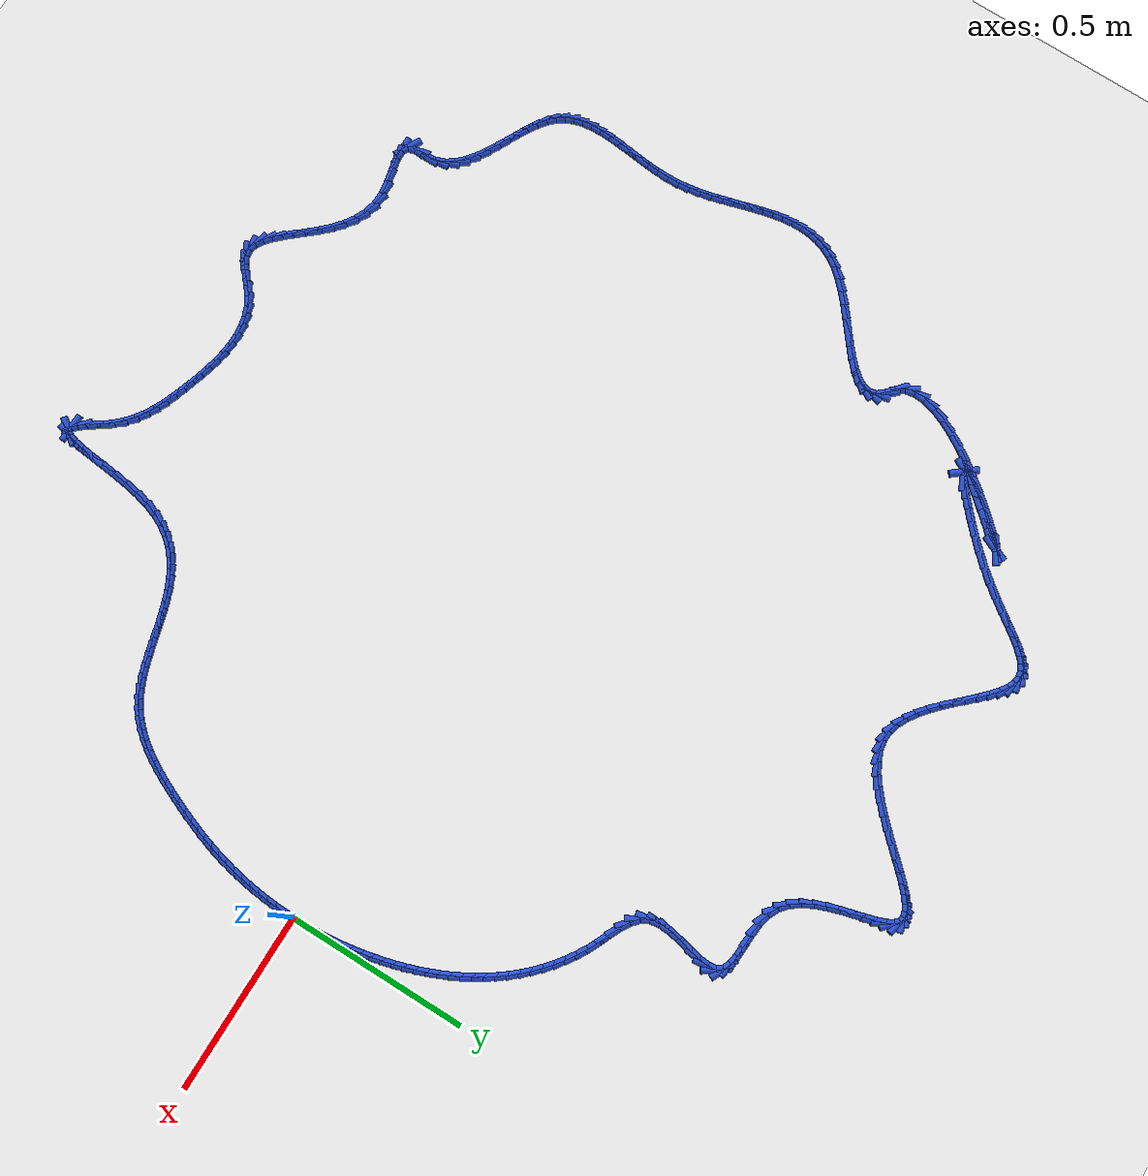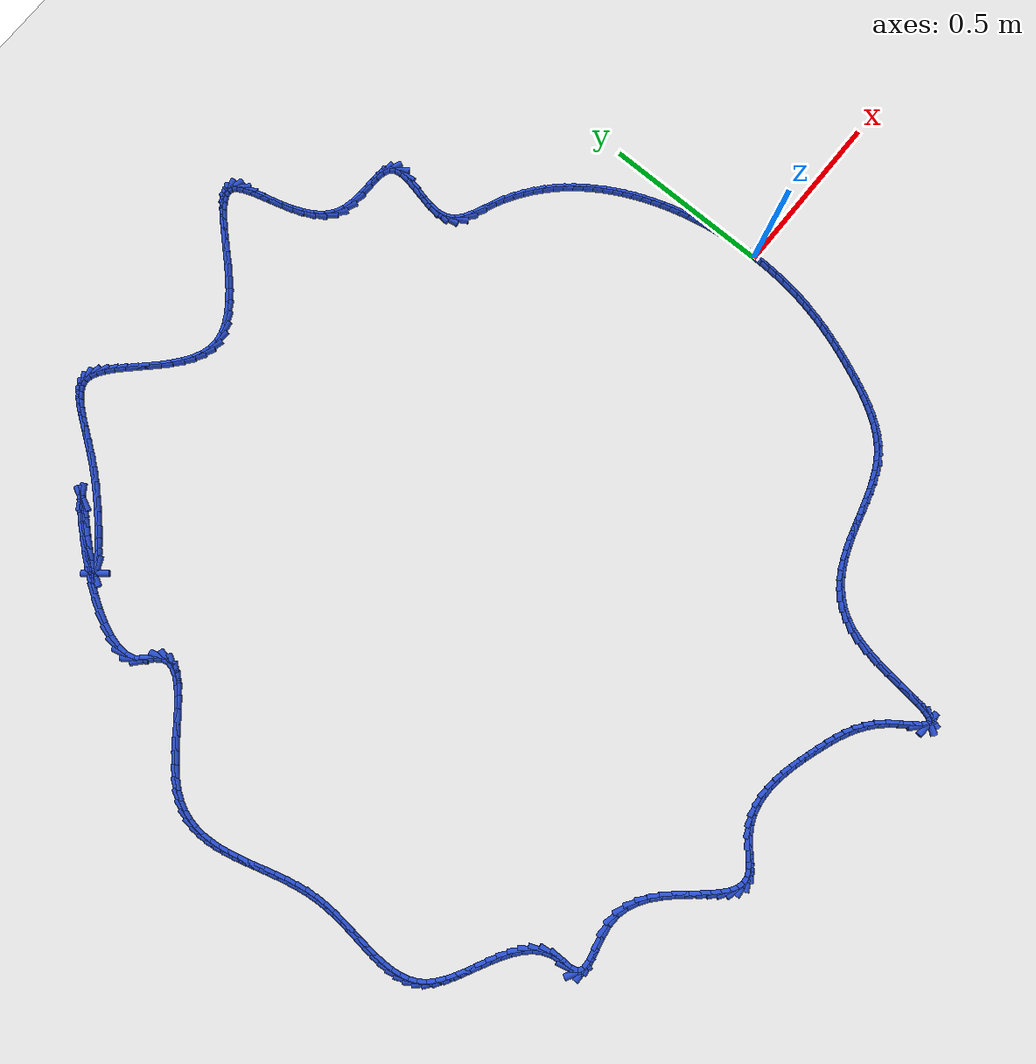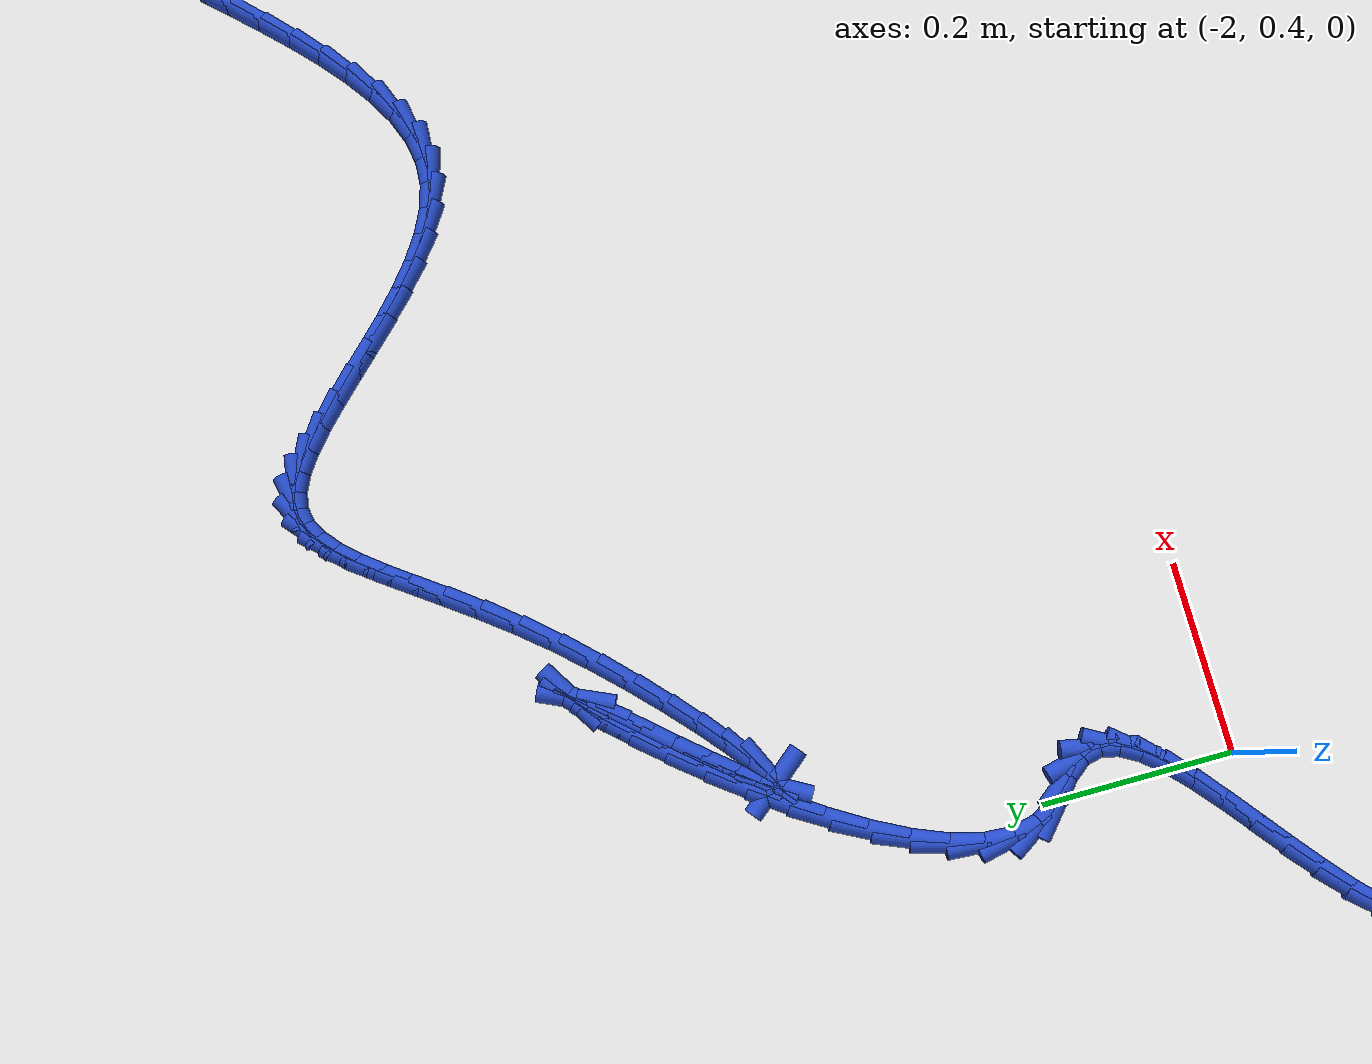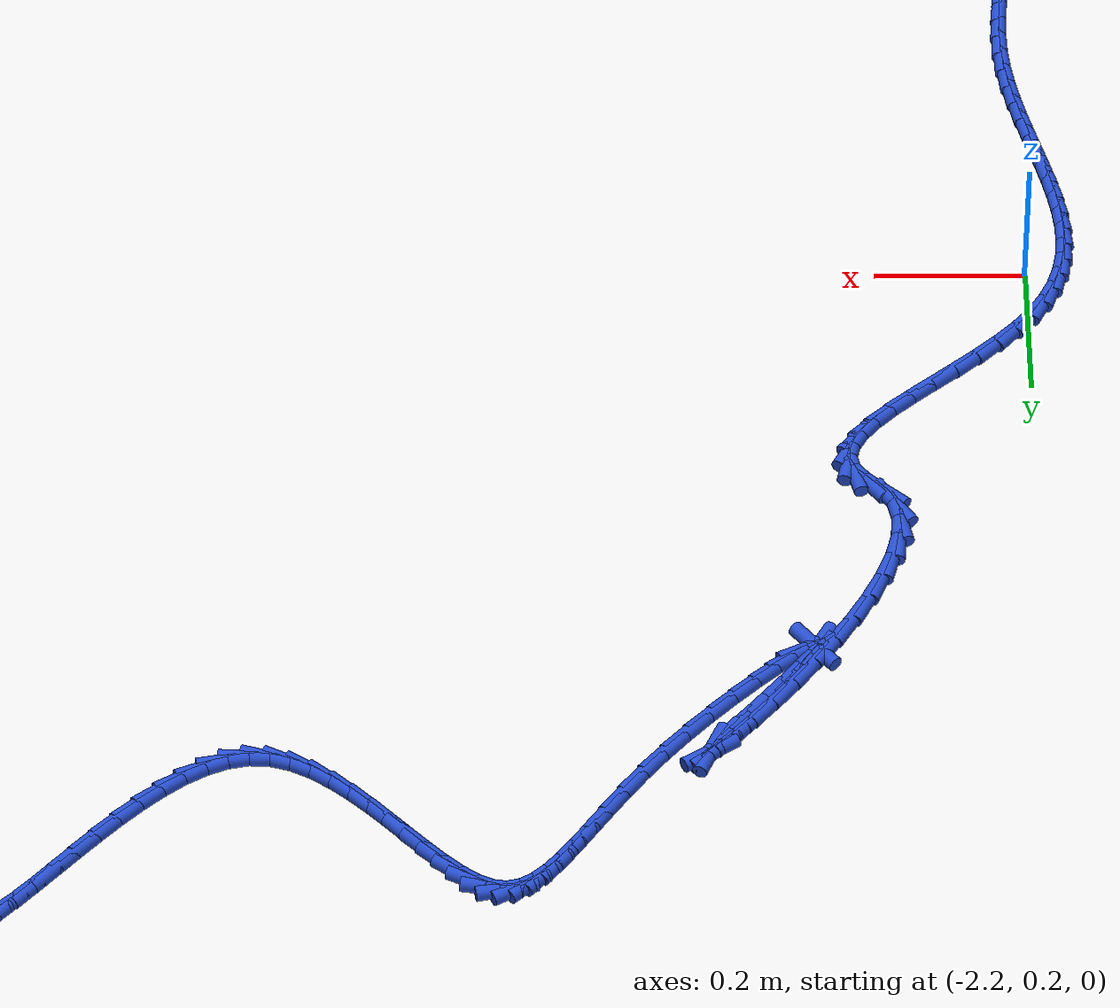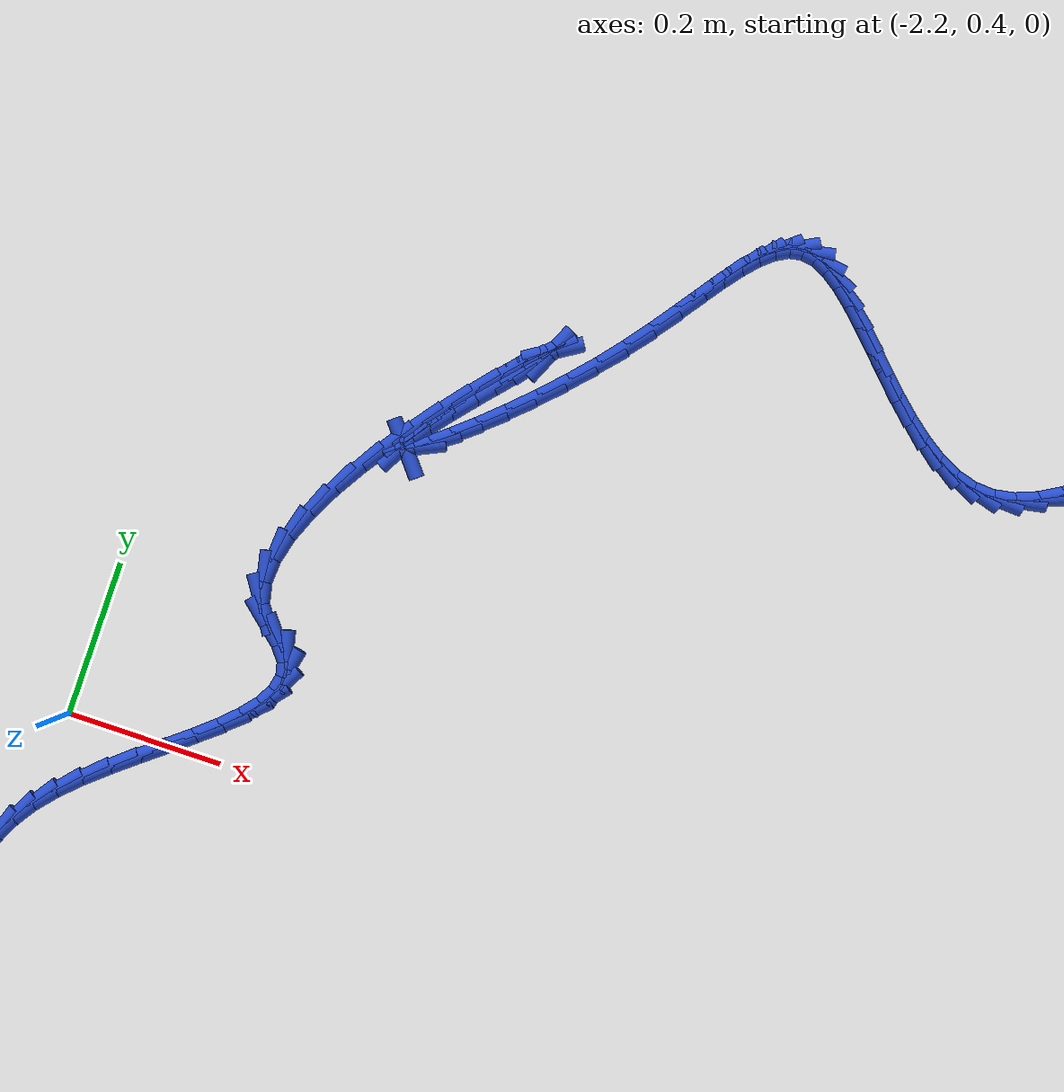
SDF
<sdf version="1.6">
 <world name="default">
  <light name="sun" type="directional">
   <pose>0 0 10 0 -0 0</pose>
   <diffuse>0.8 0.8 0.8 1</diffuse>
   <specular>0.2 0.2 0.2 1</specular>
   <attenuation>
    <range>1000</range>
    <constant>0.9</constant>
    <linear>0.01</linear>
    <quadratic>0.001</quadratic>
   </attenuation>
   <direction>-0.5 0.1 -0.9</direction>
  </light>
  <model name="ground_plane">
   <static>1</static>
   <link name="link">
    <collision name="collision">
     <geometry><plane><normal>0 0 1</normal><size>100 100</size></plane></geometry>
     <surface><friction><ode><mu>100</mu><mu2>50</mu2></ode></friction></surface>
    </collision>
    <visual name="visual">
     <cast_shadows>0</cast_shadows>
     <geometry><plane><normal>0 0 1</normal><size>100 100</size></plane></geometry>
     <material>
      <script><uri>file://media/materials/scripts/gazebo.material</uri><name>Gazebo/WhiteGlow</name></script>
     </material>
    </visual>
   </link>
  </model>
  <gravity>0 0 -9.8</gravity>
  <magnetic_field>6e-06 2.3e-05 -4.2e-05</magnetic_field>
  <atmosphere type="adiabatic"/>
  <physics name="default_physics" default="0" type="ode">
   <max_step_size>0.001</max_step_size>
   <real_time_factor>1</real_time_factor>
   <real_time_update_rate>1000</real_time_update_rate>
  </physics>
  <scene><ambient>0.4 0.4 0.4 1</ambient><background>0.7 0.7 0.7 1</background><shadows>1</shadows></scene>
  <spherical_coordinates>
   <surface_model>EARTH_WGS84</surface_model>
   <latitude_deg>0</latitude_deg>
   <longitude_deg>0</longitude_deg>
   <elevation>0</elevation>
   <heading_deg>0</heading_deg>
  </spherical_coordinates>
  <model name="line">
   <link name="link_0">
    <pose>-3.0357660829594124e-18 -2.0816681711721685e-17 0.01 0 1.57 -1.5565837611192304</pose>
    <collision name="collision">
     <geometry><cylinder><radius>0.01</radius><length>0.08</length></cylinder></geometry>
    </collision>
    <visual name="visual">
     <material>
      <script><name>Gazebo/Blue</name><uri>file://media/materials/scripts/gazebo.material</uri></script>
     </material>
     <geometry><cylinder><radius>0.01</radius><length>0.08</length></cylinder></geometry>
    </visual>
   </link>
   <link name="link_1">
    <pose>-0.0004041169483302845 0.028431864242184076 0.01 0 1.57 -1.5284859204774366</pose>
    <collision name="collision">
     <geometry><cylinder><radius>0.01</radius><length>0.08</length></cylinder></geometry>
    </collision>
    <visual name="visual">
     <material>
      <script><name>Gazebo/Blue</name><uri>file://media/materials/scripts/gazebo.material</uri></script>
     </material>
     <geometry><cylinder><radius>0.01</radius><length>0.08</length></cylinder></geometry>
    </visual>
   </link>
   <link name="link_2">
    <pose>-0.0016050707239647663 0.056799283920314324 0.01 0 1.57 -1.5001406819887342</pose>
    <collision name="collision">
     <geometry><cylinder><radius>0.01</radius><length>0.08</length></cylinder></geometry>
    </collision>
    <visual name="visual">
     <material>
      <script><name>Gazebo/Blue</name><uri>file://media/materials/scripts/gazebo.material</uri></script>
     </material>
     <geometry><cylinder><radius>0.01</radius><length>0.08</length></cylinder></geometry>
    </visual>
   </link>
   <link name="link_3">
    <pose>-0.0036085361440548755 0.08510743116033789 0.01 0 1.57 -1.4716096335745636</pose>
    <collision name="collision">
     <geometry><cylinder><radius>0.01</radius><length>0.08</length></cylinder></geometry>
    </collision>
    <visual name="visual">
     <material>
      <script><name>Gazebo/Blue</name><uri>file://media/materials/scripts/gazebo.material</uri></script>
     </material>
     <geometry><cylinder><radius>0.01</radius><length>0.08</length></cylinder></geometry>
    </visual>
   </link>
   <link name="link_4">
    <pose>-0.006420188025752031 0.11336147808820196 0.01 0 1.57 -1.442956377245693</pose>
    <collision name="collision">
     <geometry><cylinder><radius>0.01</radius><length>0.08</length></cylinder></geometry>
    </collision>
    <visual name="visual">
     <material>
      <script><name>Gazebo/Blue</name><uri>file://media/materials/scripts/gazebo.material</uri></script>
     </material>
     <geometry><cylinder><radius>0.01</radius><length>0.08</length></cylinder></geometry>
    </visual>
   </link>
   <link name="link_5">
    <pose>-0.010045701186207663 0.14156659682985365 0.01 0 1.57 -1.4142457848235797</pose>
    <collision name="collision">
     <geometry><cylinder><radius>0.01</radius><length>0.08</length></cylinder></geometry>
    </collision>
    <visual name="visual">
     <material>
      <script><name>Gazebo/Blue</name><uri>file://media/materials/scripts/gazebo.material</uri></script>
     </material>
     <geometry><cylinder><radius>0.01</radius><length>0.08</length></cylinder></geometry>
    </visual>
   </link>
   <link name="link_6">
    <pose>-0.014490750442573185 0.16972795951124003 0.01 0 1.57 -1.3855432155248486</pose>
    <collision name="collision">
     <geometry><cylinder><radius>0.01</radius><length>0.08</length></cylinder></geometry>
    </collision>
    <visual name="visual">
     <material>
      <script><name>Gazebo/Blue</name><uri>file://media/materials/scripts/gazebo.material</uri></script>
     </material>
     <geometry><cylinder><radius>0.01</radius><length>0.08</length></cylinder></geometry>
    </visual>
   </link>
   <link name="link_7">
    <pose>-0.01976101061200003 0.1978507382583084 0.01 0 1.57 -1.3569011477634403</pose>
    <collision name="collision">
     <geometry><cylinder><radius>0.01</radius><length>0.08</length></cylinder></geometry>
    </collision>
    <visual name="visual">
     <material>
      <script><name>Gazebo/Blue</name><uri>file://media/materials/scripts/gazebo.material</uri></script>
     </material>
     <geometry><cylinder><radius>0.01</radius><length>0.08</length></cylinder></geometry>
    </visual>
   </link>
   <link name="link_8">
    <pose>-0.02586236894716214 0.22593938087195514 0.01 0 1.57 -1.3278406887096128</pose>
    <collision name="collision">
     <geometry><cylinder><radius>0.01</radius><length>0.08</length></cylinder></geometry>
    </collision>
    <visual name="visual">
     <material>
      <script><name>Gazebo/Blue</name><uri>file://media/materials/scripts/gazebo.material</uri></script>
     </material>
     <geometry><cylinder><radius>0.01</radius><length>0.08</length></cylinder></geometry>
    </visual>
   </link>
   <link name="link_9">
    <pose>-0.03280944592740431 0.2539685581422681 0.01 0 1.57 -1.2975976570735104</pose>
    <collision name="collision">
     <geometry><cylinder><radius>0.01</radius><length>0.08</length></cylinder></geometry>
    </collision>
    <visual name="visual">
     <material>
      <script><name>Gazebo/Blue</name><uri>file://media/materials/scripts/gazebo.material</uri></script>
     </material>
     <geometry><cylinder><radius>0.01</radius><length>0.08</length></cylinder></geometry>
    </visual>
   </link>
   <link name="link_10">
    <pose>-0.04062848938661211 0.28187329596348015 0.01 0 1.57 -1.2660096918511405</pose>
    <collision name="collision">
     <geometry><cylinder><radius>0.01</radius><length>0.08</length></cylinder></geometry>
    </collision>
    <visual name="visual">
     <material>
      <script><name>Gazebo/Blue</name><uri>file://media/materials/scripts/gazebo.material</uri></script>
     </material>
     <geometry><cylinder><radius>0.01</radius><length>0.08</length></cylinder></geometry>
    </visual>
   </link>
   <link name="link_11">
    <pose>-0.049346553325772154 0.3095858715039086 0.01 0 1.57 -1.2329635797595693</pose>
    <collision name="collision">
     <geometry><cylinder><radius>0.01</radius><length>0.08</length></cylinder></geometry>
    </collision>
    <visual name="visual">
     <material>
      <script><name>Gazebo/Blue</name><uri>file://media/materials/scripts/gazebo.material</uri></script>
     </material>
     <geometry><cylinder><radius>0.01</radius><length>0.08</length></cylinder></geometry>
    </visual>
   </link>
   <link name="link_12">
    <pose>-0.058990691745871036 0.3370385619318703 0.01 0 1.57 -1.1983488932502169</pose>
    <collision name="collision">
     <geometry><cylinder><radius>0.01</radius><length>0.08</length></cylinder></geometry>
    </collision>
    <visual name="visual">
     <material>
      <script><name>Gazebo/Blue</name><uri>file://media/materials/scripts/gazebo.material</uri></script>
     </material>
     <geometry><cylinder><radius>0.01</radius><length>0.08</length></cylinder></geometry>
    </visual>
   </link>
   <link name="link_13">
    <pose>-0.06958795864789534 0.36416364441568255 0.01 0 1.57 -1.1620599497109119</pose>
    <collision name="collision">
     <geometry><cylinder><radius>0.01</radius><length>0.08</length></cylinder></geometry>
    </collision>
    <visual name="visual">
     <material>
      <script><name>Gazebo/Blue</name><uri>file://media/materials/scripts/gazebo.material</uri></script>
     </material>
     <geometry><cylinder><radius>0.01</radius><length>0.08</length></cylinder></geometry>
    </visual>
   </link>
   <link name="link_14">
    <pose>-0.08116540803283172 0.39089339612366225 0.01 0 1.57 -1.1239984541088368</pose>
    <collision name="collision">
     <geometry><cylinder><radius>0.01</radius><length>0.08</length></cylinder></geometry>
    </collision>
    <visual name="visual">
     <material>
      <script><name>Gazebo/Blue</name><uri>file://media/materials/scripts/gazebo.material</uri></script>
     </material>
     <geometry><cylinder><radius>0.01</radius><length>0.08</length></cylinder></geometry>
    </visual>
   </link>
   <link name="link_15">
    <pose>-0.09375009390166672 0.41716009422412653 0.01 0 1.57 -1.0840768847911435</pose>
    <collision name="collision">
     <geometry><cylinder><radius>0.01</radius><length>0.08</length></cylinder></geometry>
    </collision>
    <visual name="visual">
     <material>
      <script><name>Gazebo/Blue</name><uri>file://media/materials/scripts/gazebo.material</uri></script>
     </material>
     <geometry><cylinder><radius>0.01</radius><length>0.08</length></cylinder></geometry>
    </visual>
   </link>
   <link name="link_16">
    <pose>-0.10736907025538697 0.44289601588539246 0.01 0 1.57 -1.0422226506803636</pose>
    <collision name="collision">
     <geometry><cylinder><radius>0.01</radius><length>0.08</length></cylinder></geometry>
    </collision>
    <visual name="visual">
     <material>
      <script><name>Gazebo/Blue</name><uri>file://media/materials/scripts/gazebo.material</uri></script>
     </material>
     <geometry><cylinder><radius>0.01</radius><length>0.08</length></cylinder></geometry>
    </visual>
   </link>
   <link name="link_17">
    <pose>-0.12204939109497907 0.46803343827577715 0.01 0 1.57 -0.9983829927983333</pose>
    <collision name="collision">
     <geometry><cylinder><radius>0.01</radius><length>0.08</length></cylinder></geometry>
    </collision>
    <visual name="visual">
     <material>
      <script><name>Gazebo/Blue</name><uri>file://media/materials/scripts/gazebo.material</uri></script>
     </material>
     <geometry><cylinder><radius>0.01</radius><length>0.08</length></cylinder></geometry>
    </visual>
   </link>
   <link name="link_18">
    <pose>-0.13781811042142963 0.4925046385635976 0.01 0 1.57 -0.9525305192763821</pose>
    <collision name="collision">
     <geometry><cylinder><radius>0.01</radius><length>0.08</length></cylinder></geometry>
    </collision>
    <visual name="visual">
     <material>
      <script><name>Gazebo/Blue</name><uri>file://media/materials/scripts/gazebo.material</uri></script>
     </material>
     <geometry><cylinder><radius>0.01</radius><length>0.08</length></cylinder></geometry>
    </visual>
   </link>
   <link name="link_19">
    <pose>-0.15470228223572524 0.5162418939171709 0.01 0 1.57 -0.9046691493081778</pose>
    <collision name="collision">
     <geometry><cylinder><radius>0.01</radius><length>0.08</length></cylinder></geometry>
    </collision>
    <visual name="visual">
     <material>
      <script><name>Gazebo/Blue</name><uri>file://media/materials/scripts/gazebo.material</uri></script>
     </material>
     <geometry><cylinder><radius>0.01</radius><length>0.08</length></cylinder></geometry>
    </visual>
   </link>
   <link name="link_20">
    <pose>-0.17272896053885256 0.5391774815048141 0.01 0 1.57 -0.8548401026462458</pose>
    <collision name="collision">
     <geometry><cylinder><radius>0.01</radius><length>0.08</length></cylinder></geometry>
    </collision>
    <visual name="visual">
     <material>
      <script><name>Gazebo/Blue</name><uri>file://media/materials/scripts/gazebo.material</uri></script>
     </material>
     <geometry><cylinder><radius>0.01</radius><length>0.08</length></cylinder></geometry>
    </visual>
   </link>
   <link name="link_21">
    <pose>-0.19192519933179808 0.5612436784948442 0.01 0 1.57 -0.8031274215292697</pose>
    <collision name="collision">
     <geometry><cylinder><radius>0.01</radius><length>0.08</length></cylinder></geometry>
    </collision>
    <visual name="visual">
     <material>
      <script><name>Gazebo/Blue</name><uri>file://media/materials/scripts/gazebo.material</uri></script>
     </material>
     <geometry><cylinder><radius>0.01</radius><length>0.08</length></cylinder></geometry>
    </visual>
   </link>
   <link name="link_22">
    <pose>-0.21231805261554848 0.5823727620555786 0.01 0 1.57 -0.7496623774940291</pose>
    <collision name="collision">
     <geometry><cylinder><radius>0.01</radius><length>0.08</length></cylinder></geometry>
    </collision>
    <visual name="visual">
     <material>
      <script><name>Gazebo/Blue</name><uri>file://media/materials/scripts/gazebo.material</uri></script>
     </material>
     <geometry><cylinder><radius>0.01</radius><length>0.08</length></cylinder></geometry>
    </visual>
   </link>
   <link name="link_23">
    <pose>-0.23393457439109025 0.6024970093553339 0.01 0 1.57 -0.6946260337252137</pose>
    <collision name="collision">
     <geometry><cylinder><radius>0.01</radius><length>0.08</length></cylinder></geometry>
    </collision>
    <visual name="visual">
     <material>
      <script><name>Gazebo/Blue</name><uri>file://media/materials/scripts/gazebo.material</uri></script>
     </material>
     <geometry><cylinder><radius>0.01</radius><length>0.08</length></cylinder></geometry>
    </visual>
   </link>
   <link name="link_24">
    <pose>-0.25680181865941026 0.6215486975624275 0.01 0 1.57 -0.6382492472792084</pose>
    <collision name="collision">
     <geometry><cylinder><radius>0.01</radius><length>0.08</length></cylinder></geometry>
    </collision>
    <visual name="visual">
     <material>
      <script><name>Gazebo/Blue</name><uri>file://media/materials/scripts/gazebo.material</uri></script>
     </material>
     <geometry><cylinder><radius>0.01</radius><length>0.08</length></cylinder></geometry>
    </visual>
   </link>
   <link name="link_25">
    <pose>-0.2809468394214949 0.6394601038451766 0.01 0 1.57 -0.5808095412042004</pose>
    <collision name="collision">
     <geometry><cylinder><radius>0.01</radius><length>0.08</length></cylinder></geometry>
    </collision>
    <visual name="visual">
     <material>
      <script><name>Gazebo/Blue</name><uri>file://media/materials/scripts/gazebo.material</uri></script>
     </material>
     <geometry><cylinder><radius>0.01</radius><length>0.08</length></cylinder></geometry>
    </visual>
   </link>
   <link name="link_26">
    <pose>-0.3063966906783307 0.6561635053718976 0.01 0 1.57 -0.522624568244136</pose>
    <collision name="collision">
     <geometry><cylinder><radius>0.01</radius><length>0.08</length></cylinder></geometry>
    </collision>
    <visual name="visual">
     <material>
      <script><name>Gazebo/Blue</name><uri>file://media/materials/scripts/gazebo.material</uri></script>
     </material>
     <geometry><cylinder><radius>0.01</radius><length>0.08</length></cylinder></geometry>
    </visual>
   </link>
   <link name="link_27">
    <pose>-0.3331784264309044 0.6715911793109082 0.01 0 1.57 -0.46404230185552214</pose>
    <collision name="collision">
     <geometry><cylinder><radius>0.01</radius><length>0.08</length></cylinder></geometry>
    </collision>
    <visual name="visual">
     <material>
      <script><name>Gazebo/Blue</name><uri>file://media/materials/scripts/gazebo.material</uri></script>
     </material>
     <geometry><cylinder><radius>0.01</radius><length>0.08</length></cylinder></geometry>
    </visual>
   </link>
   <link name="link_28">
    <pose>-0.3613191006802027 0.6856754028305252 0.01 0 1.57 -0.41724257743790666</pose>
    <collision name="collision">
     <geometry><cylinder><radius>0.01</radius><length>0.08</length></cylinder></geometry>
    </collision>
    <visual name="visual">
     <material>
      <script><name>Gazebo/Blue</name><uri>file://media/materials/scripts/gazebo.material</uri></script>
     </material>
     <geometry><cylinder><radius>0.01</radius><length>0.08</length></cylinder></geometry>
    </visual>
   </link>
   <link name="link_29">
    <pose>-0.3904823503910066 0.6986025754839386 0.01 0 1.57 -0.42921007259932664</pose>
    <collision name="collision">
     <geometry><cylinder><radius>0.01</radius><length>0.08</length></cylinder></geometry>
    </collision>
    <visual name="visual">
     <material>
      <script><name>Gazebo/Blue</name><uri>file://media/materials/scripts/gazebo.material</uri></script>
     </material>
     <geometry><cylinder><radius>0.01</radius><length>0.08</length></cylinder></geometry>
    </visual>
   </link>
   <link name="link_30">
    <pose>-0.41885847279085736 0.7115893418884229 0.01 0 1.57 -0.5193345825374572</pose>
    <collision name="collision">
     <geometry><cylinder><radius>0.01</radius><length>0.08</length></cylinder></geometry>
    </collision>
    <visual name="visual">
     <material>
      <script><name>Gazebo/Blue</name><uri>file://media/materials/scripts/gazebo.material</uri></script>
     </material>
     <geometry><cylinder><radius>0.01</radius><length>0.08</length></cylinder></geometry>
    </visual>
   </link>
   <link name="link_31">
    <pose>-0.44426444590678676 0.7261133932168655 0.01 0 1.57 -0.7137127139691173</pose>
    <collision name="collision">
     <geometry><cylinder><radius>0.01</radius><length>0.08</length></cylinder></geometry>
    </collision>
    <visual name="visual">
     <material>
      <script><name>Gazebo/Blue</name><uri>file://media/materials/scripts/gazebo.material</uri></script>
     </material>
     <geometry><cylinder><radius>0.01</radius><length>0.08</length></cylinder></geometry>
    </visual>
   </link>
   <link name="link_32">
    <pose>-0.4645172477326955 0.7436524206653207 0.01 0 1.57 -1.0403992607029242</pose>
    <collision name="collision">
     <geometry><cylinder><radius>0.01</radius><length>0.08</length></cylinder></geometry>
    </collision>
    <visual name="visual">
     <material>
      <script><name>Gazebo/Blue</name><uri>file://media/materials/scripts/gazebo.material</uri></script>
     </material>
     <geometry><cylinder><radius>0.01</radius><length>0.08</length></cylinder></geometry>
    </visual>
   </link>
   <link name="link_33">
    <pose>-0.4774366080567777 0.7656821742264766 0.01 0 1.57 -1.4039612263122339</pose>
    <collision name="collision">
     <geometry><cylinder><radius>0.01</radius><length>0.08</length></cylinder></geometry>
    </collision>
    <visual name="visual">
     <material>
      <script><name>Gazebo/Blue</name><uri>file://media/materials/scripts/gazebo.material</uri></script>
     </material>
     <geometry><cylinder><radius>0.01</radius><length>0.08</length></cylinder></geometry>
    </visual>
   </link>
   <link name="link_34">
    <pose>-0.48201220138556805 0.7928530876144257 0.01 0 1.57 1.5126866364312026</pose>
    <collision name="collision">
     <geometry><cylinder><radius>0.01</radius><length>0.08</length></cylinder></geometry>
    </collision>
    <visual name="visual">
     <material>
      <script><name>Gazebo/Blue</name><uri>file://media/materials/scripts/gazebo.material</uri></script>
     </material>
     <geometry><cylinder><radius>0.01</radius><length>0.08</length></cylinder></geometry>
    </visual>
   </link>
   <link name="link_35">
    <pose>-0.48021703323472115 0.8237110578009157 0.01 0 1.57 1.3978102307360205</pose>
    <collision name="collision">
     <geometry><cylinder><radius>0.01</radius><length>0.08</length></cylinder></geometry>
    </collision>
    <visual name="visual">
     <material>
      <script><name>Gazebo/Blue</name><uri>file://media/materials/scripts/gazebo.material</uri></script>
     </material>
     <geometry><cylinder><radius>0.01</radius><length>0.08</length></cylinder></geometry>
    </visual>
   </link>
   <link name="link_36">
    <pose>-0.47449273764229405 0.8564713962675495 0.01 0 1.57 1.3548662235397153</pose>
    <collision name="collision">
     <geometry><cylinder><radius>0.01</radius><length>0.08</length></cylinder></geometry>
    </collision>
    <visual name="visual">
     <material>
      <script><name>Gazebo/Blue</name><uri>file://media/materials/scripts/gazebo.material</uri></script>
     </material>
     <geometry><cylinder><radius>0.01</radius><length>0.08</length></cylinder></geometry>
    </visual>
   </link>
   <link name="link_37">
    <pose>-0.4672809486463442 0.8893494144959311 0.01 0 1.57 1.3729249426160999</pose>
    <collision name="collision">
     <geometry><cylinder><radius>0.01</radius><length>0.08</length></cylinder></geometry>
    </collision>
    <visual name="visual">
     <material>
      <script><name>Gazebo/Blue</name><uri>file://media/materials/scripts/gazebo.material</uri></script>
     </material>
     <geometry><cylinder><radius>0.01</radius><length>0.08</length></cylinder></geometry>
    </visual>
   </link>
   <link name="link_38">
    <pose>-0.46102330028492894 0.920560423967663 0.01 0 1.57 1.4680632895905692</pose>
    <collision name="collision">
     <geometry><cylinder><radius>0.01</radius><length>0.08</length></cylinder></geometry>
    </collision>
    <visual name="visual">
     <material>
      <script><name>Gazebo/Blue</name><uri>file://media/materials/scripts/gazebo.material</uri></script>
     </material>
     <geometry><cylinder><radius>0.01</radius><length>0.08</length></cylinder></geometry>
    </visual>
   </link>
   <link name="link_39">
    <pose>-0.45816142659610537 0.9483197361643496 0.01 0 1.57 -1.4394455895109424</pose>
    <collision name="collision">
     <geometry><cylinder><radius>0.01</radius><length>0.08</length></cylinder></geometry>
    </collision>
    <visual name="visual">
     <material>
      <script><name>Gazebo/Blue</name><uri>file://media/materials/scripts/gazebo.material</uri></script>
     </material>
     <geometry><cylinder><radius>0.01</radius><length>0.08</length></cylinder></geometry>
    </visual>
   </link>
   <link name="link_40">
    <pose>-0.4611369616179312 0.9708426625675943 0.01 0 1.57 -0.9482673424361193</pose>
    <collision name="collision">
     <geometry><cylinder><radius>0.01</radius><length>0.08</length></cylinder></geometry>
    </collision>
    <visual name="visual">
     <material>
      <script><name>Gazebo/Blue</name><uri>file://media/materials/scripts/gazebo.material</uri></script>
     </material>
     <geometry><cylinder><radius>0.01</radius><length>0.08</length></cylinder></geometry>
    </visual>
   </link>
   <link name="link_41">
    <pose>-0.472312769322741 0.9864136264071249 0.01 0 1.57 -0.41811912800754447</pose>
    <collision name="collision">
     <geometry><cylinder><radius>0.01</radius><length>0.08</length></cylinder></geometry>
    </collision>
    <visual name="visual">
     <material>
      <script><name>Gazebo/Blue</name><uri>file://media/materials/scripts/gazebo.material</uri></script>
     </material>
     <geometry><cylinder><radius>0.01</radius><length>0.08</length></cylinder></geometry>
    </visual>
   </link>
   <link name="link_42">
    <pose>-0.4919668375662989 0.9951462919031011 0.01 0 1.57 -0.15102178992092483</pose>
    <collision name="collision">
     <geometry><cylinder><radius>0.01</radius><length>0.08</length></cylinder></geometry>
    </collision>
    <visual name="visual">
     <material>
      <script><name>Gazebo/Blue</name><uri>file://media/materials/scripts/gazebo.material</uri></script>
     </material>
     <geometry><cylinder><radius>0.01</radius><length>0.08</length></cylinder></geometry>
    </visual>
   </link>
   <link name="link_43">
    <pose>-0.518128183206521 0.9991275388077032 0.01 0 1.57 -0.04621916691536989</pose>
    <collision name="collision">
     <geometry><cylinder><radius>0.01</radius><length>0.08</length></cylinder></geometry>
    </collision>
    <visual name="visual">
     <material>
      <script><name>Gazebo/Blue</name><uri>file://media/materials/scripts/gazebo.material</uri></script>
     </material>
     <geometry><cylinder><radius>0.01</radius><length>0.08</length></cylinder></geometry>
    </visual>
   </link>
   <link name="link_44">
    <pose>-0.5487141749934646 1.0005422053531277 0.01 0 1.57 -0.03135889215472687</pose>
    <collision name="collision">
     <geometry><cylinder><radius>0.01</radius><length>0.08</length></cylinder></geometry>
    </collision>
    <visual name="visual">
     <material>
      <script><name>Gazebo/Blue</name><uri>file://media/materials/scripts/gazebo.material</uri></script>
     </material>
     <geometry><cylinder><radius>0.01</radius><length>0.08</length></cylinder></geometry>
    </visual>
   </link>
   <link name="link_45">
    <pose>-0.5816421816771867 1.0015751297715705 0.01 0 1.57 -0.08524765652726708</pose>
    <collision name="collision">
     <geometry><cylinder><radius>0.01</radius><length>0.08</length></cylinder></geometry>
    </collision>
    <visual name="visual">
     <material>
      <script><name>Gazebo/Blue</name><uri>file://media/materials/scripts/gazebo.material</uri></script>
     </material>
     <geometry><cylinder><radius>0.01</radius><length>0.08</length></cylinder></geometry>
    </visual>
   </link>
   <link name="link_46">
    <pose>-0.6148295720077435 1.0044111502952289 0.01 0 1.57 -0.21423308464687127</pose>
    <collision name="collision">
     <geometry><cylinder><radius>0.01</radius><length>0.08</length></cylinder></geometry>
    </collision>
    <visual name="visual">
     <material>
      <script><name>Gazebo/Blue</name><uri>file://media/materials/scripts/gazebo.material</uri></script>
     </material>
     <geometry><cylinder><radius>0.01</radius><length>0.08</length></cylinder></geometry>
    </visual>
   </link>
   <link name="link_47">
    <pose>-0.646193714735192 1.0112351051562987 0.01 0 1.57 -0.4393105872193635</pose>
    <collision name="collision">
     <geometry><cylinder><radius>0.01</radius><length>0.08</length></cylinder></geometry>
    </collision>
    <visual name="visual">
     <material>
      <script><name>Gazebo/Blue</name><uri>file://media/materials/scripts/gazebo.material</uri></script>
     </material>
     <geometry><cylinder><radius>0.01</radius><length>0.08</length></cylinder></geometry>
    </visual>
   </link>
   <link name="link_48">
    <pose>-0.6737044519141393 1.0241634621988427 0.01 0 1.57 -0.7045980109727769</pose>
    <collision name="collision">
     <geometry><cylinder><radius>0.01</radius><length>0.08</length></cylinder></geometry>
    </collision>
    <visual name="visual">
     <material>
      <script><name>Gazebo/Blue</name><uri>file://media/materials/scripts/gazebo.material</uri></script>
     </material>
     <geometry><cylinder><radius>0.01</radius><length>0.08</length></cylinder></geometry>
    </visual>
   </link>
   <link name="link_49">
    <pose>-0.6966145257263477 1.0436411273101704 0.01 0 1.57 -0.9187825900491353</pose>
    <collision name="collision">
     <geometry><cylinder><radius>0.01</radius><length>0.08</length></cylinder></geometry>
    </collision>
    <visual name="visual">
     <material>
      <script><name>Gazebo/Blue</name><uri>file://media/materials/scripts/gazebo.material</uri></script>
     </material>
     <geometry><cylinder><radius>0.01</radius><length>0.08</length></cylinder></geometry>
    </visual>
   </link>
   <link name="link_50">
    <pose>-0.7155032858335693 1.0683844956789388 0.01 0 1.57 -1.0746005450745542</pose>
    <collision name="collision">
     <geometry><cylinder><radius>0.01</radius><length>0.08</length></cylinder></geometry>
    </collision>
    <visual name="visual">
     <material>
      <script><name>Gazebo/Blue</name><uri>file://media/materials/scripts/gazebo.material</uri></script>
     </material>
     <geometry><cylinder><radius>0.01</radius><length>0.08</length></cylinder></geometry>
    </visual>
   </link>
   <link name="link_51">
    <pose>-0.7310112997483827 1.097030198349777 0.01 0 1.57 -1.182190004740575</pose>
    <collision name="collision">
     <geometry><cylinder><radius>0.01</radius><length>0.08</length></cylinder></geometry>
    </collision>
    <visual name="visual">
     <material>
      <script><name>Gazebo/Blue</name><uri>file://media/materials/scripts/gazebo.material</uri></script>
     </material>
     <geometry><cylinder><radius>0.01</radius><length>0.08</length></cylinder></geometry>
    </visual>
   </link>
   <link name="link_52">
    <pose>-0.7437791349833669 1.1282148663673142 0.01 0 1.57 -1.2523459501971252</pose>
    <collision name="collision">
     <geometry><cylinder><radius>0.01</radius><length>0.08</length></cylinder></geometry>
    </collision>
    <visual name="visual">
     <material>
      <script><name>Gazebo/Blue</name><uri>file://media/materials/scripts/gazebo.material</uri></script>
     </material>
     <geometry><cylinder><radius>0.01</radius><length>0.08</length></cylinder></geometry>
    </visual>
   </link>
   <link name="link_53">
    <pose>-0.7544473590511 1.1605751307761782 0.01 0 1.57 -1.2920070677949385</pose>
    <collision name="collision">
     <geometry><cylinder><radius>0.01</radius><length>0.08</length></cylinder></geometry>
    </collision>
    <visual name="visual">
     <material>
      <script><name>Gazebo/Blue</name><uri>file://media/materials/scripts/gazebo.material</uri></script>
     </material>
     <geometry><cylinder><radius>0.01</radius><length>0.08</length></cylinder></geometry>
    </visual>
   </link>
   <link name="link_54">
    <pose>-0.7636565394641612 1.1927476226209992 0.01 0 1.57 -1.3033462460114438</pose>
    <collision name="collision">
     <geometry><cylinder><radius>0.01</radius><length>0.08</length></cylinder></geometry>
    </collision>
    <visual name="visual">
     <material>
      <script><name>Gazebo/Blue</name><uri>file://media/materials/scripts/gazebo.material</uri></script>
     </material>
     <geometry><cylinder><radius>0.01</radius><length>0.08</length></cylinder></geometry>
    </visual>
   </link>
   <link name="link_55">
    <pose>-0.7720472437351287 1.2233689729464048 0.01 0 1.57 -1.2826293474768657</pose>
    <collision name="collision">
     <geometry><cylinder><radius>0.01</radius><length>0.08</length></cylinder></geometry>
    </collision>
    <visual name="visual">
     <material>
      <script><name>Gazebo/Blue</name><uri>file://media/materials/scripts/gazebo.material</uri></script>
     </material>
     <geometry><cylinder><radius>0.01</radius><length>0.08</length></cylinder></geometry>
    </visual>
   </link>
   <link name="link_56">
    <pose>-0.7802600393765811 1.2510758127970247 0.01 0 1.57 -1.2161634252203724</pose>
    <collision name="collision">
     <geometry><cylinder><radius>0.01</radius><length>0.08</length></cylinder></geometry>
    </collision>
    <visual name="visual">
     <material>
      <script><name>Gazebo/Blue</name><uri>file://media/materials/scripts/gazebo.material</uri></script>
     </material>
     <geometry><cylinder><radius>0.01</radius><length>0.08</length></cylinder></geometry>
    </visual>
   </link>
   <link name="link_57">
    <pose>-0.7889354939010971 1.2745047732174875 0.01 0 1.57 -1.0681499863516444</pose>
    <collision name="collision">
     <geometry><cylinder><radius>0.01</radius><length>0.08</length></cylinder></geometry>
    </collision>
    <visual name="visual">
     <material>
      <script><name>Gazebo/Blue</name><uri>file://media/materials/scripts/gazebo.material</uri></script>
     </material>
     <geometry><cylinder><radius>0.01</radius><length>0.08</length></cylinder></geometry>
    </visual>
   </link>
   <link name="link_58">
    <pose>-0.7987141748212554 1.292292485252422 0.01 0 1.57 -0.7525650326597283</pose>
    <collision name="collision">
     <geometry><cylinder><radius>0.01</radius><length>0.08</length></cylinder></geometry>
    </collision>
    <visual name="visual">
     <material>
      <script><name>Gazebo/Blue</name><uri>file://media/materials/scripts/gazebo.material</uri></script>
     </material>
     <geometry><cylinder><radius>0.01</radius><length>0.08</length></cylinder></geometry>
    </visual>
   </link>
   <link name="link_59">
    <pose>-0.8102349196840257 1.3030805003656218 0.01 0 1.57 -0.22488775656847576</pose>
    <collision name="collision">
     <geometry><cylinder><radius>0.01</radius><length>0.08</length></cylinder></geometry>
    </collision>
    <visual name="visual">
     <material>
      <script><name>Gazebo/Blue</name><uri>file://media/materials/scripts/gazebo.material</uri></script>
     </material>
     <geometry><cylinder><radius>0.01</radius><length>0.08</length></cylinder></geometry>
    </visual>
   </link>
   <link name="link_60">
    <pose>-0.8238924280675783 1.3062047544260817 0.01 0 1.57 0.2374343966636377</pose>
    <collision name="collision">
     <geometry><cylinder><radius>0.01</radius><length>0.08</length></cylinder></geometry>
    </collision>
    <visual name="visual">
     <material>
      <script><name>Gazebo/Blue</name><uri>file://media/materials/scripts/gazebo.material</uri></script>
     </material>
     <geometry><cylinder><radius>0.01</radius><length>0.08</length></cylinder></geometry>
    </visual>
   </link>
   <link name="link_61">
    <pose>-0.8395872643099407 1.3024066173141675 0.01 0 1.57 0.5091245140428687</pose>
    <collision name="collision">
     <geometry><cylinder><radius>0.01</radius><length>0.08</length></cylinder></geometry>
    </collision>
    <visual name="visual">
     <material>
      <script><name>Gazebo/Blue</name><uri>file://media/materials/scripts/gazebo.material</uri></script>
     </material>
     <geometry><cylinder><radius>0.01</radius><length>0.08</length></cylinder></geometry>
    </visual>
   </link>
   <link name="link_62">
    <pose>-0.8571603277364145 1.292597159897663 0.01 0 1.57 0.6579569372778699</pose>
    <collision name="collision">
     <geometry><cylinder><radius>0.01</radius><length>0.08</length></cylinder></geometry>
    </collision>
    <visual name="visual">
     <material>
      <script><name>Gazebo/Blue</name><uri>file://media/materials/scripts/gazebo.material</uri></script>
     </material>
     <geometry><cylinder><radius>0.01</radius><length>0.08</length></cylinder></geometry>
    </visual>
   </link>
   <link name="link_63">
    <pose>-0.8764525176723037 1.277687453044352 0.01 0 1.57 0.7415393980212701</pose>
    <collision name="collision">
     <geometry><cylinder><radius>0.01</radius><length>0.08</length></cylinder></geometry>
    </collision>
    <visual name="visual">
     <material>
      <script><name>Gazebo/Blue</name><uri>file://media/materials/scripts/gazebo.material</uri></script>
     </material>
     <geometry><cylinder><radius>0.01</radius><length>0.08</length></cylinder></geometry>
    </visual>
   </link>
   <link name="link_64">
    <pose>-0.897304733442911 1.2585885676220179 0.01 0 1.57 0.7881732362857409</pose>
    <collision name="collision">
     <geometry><cylinder><radius>0.01</radius><length>0.08</length></cylinder></geometry>
    </collision>
    <visual name="visual">
     <material>
      <script><name>Gazebo/Blue</name><uri>file://media/materials/scripts/gazebo.material</uri></script>
     </material>
     <geometry><cylinder><radius>0.01</radius><length>0.08</length></cylinder></geometry>
    </visual>
   </link>
   <link name="link_65">
    <pose>-0.9195578743735394 1.2362115744984448 0.01 0 1.57 0.8112856325320796</pose>
    <collision name="collision">
     <geometry><cylinder><radius>0.01</radius><length>0.08</length></cylinder></geometry>
    </collision>
    <visual name="visual">
     <material>
      <script><name>Gazebo/Blue</name><uri>file://media/materials/scripts/gazebo.material</uri></script>
     </material>
     <geometry><cylinder><radius>0.01</radius><length>0.08</length></cylinder></geometry>
    </visual>
   </link>
   <link name="link_66">
    <pose>-0.9430528397894921 1.2114675445414167 0.01 0 1.57 0.8173365047847124</pose>
    <collision name="collision">
     <geometry><cylinder><radius>0.01</radius><length>0.08</length></cylinder></geometry>
    </collision>
    <visual name="visual">
     <material>
      <script><name>Gazebo/Blue</name><uri>file://media/materials/scripts/gazebo.material</uri></script>
     </material>
     <geometry><cylinder><radius>0.01</radius><length>0.08</length></cylinder></geometry>
    </visual>
   </link>
   <link name="link_67">
    <pose>-0.9676305290160714 1.1852675486187167 0.01 0 1.57 0.8091959478905993</pose>
    <collision name="collision">
     <geometry><cylinder><radius>0.01</radius><length>0.08</length></cylinder></geometry>
    </collision>
    <visual name="visual">
     <material>
      <script><name>Gazebo/Blue</name><uri>file://media/materials/scripts/gazebo.material</uri></script>
     </material>
     <geometry><cylinder><radius>0.01</radius><length>0.08</length></cylinder></geometry>
    </visual>
   </link>
   <link name="link_68">
    <pose>-0.993131841378581 1.1585226575981282 0.01 0 1.57 0.7875423597823953</pose>
    <collision name="collision">
     <geometry><cylinder><radius>0.01</radius><length>0.08</length></cylinder></geometry>
    </collision>
    <visual name="visual">
     <material>
      <script><name>Gazebo/Blue</name><uri>file://media/materials/scripts/gazebo.material</uri></script>
     </material>
     <geometry><cylinder><radius>0.01</radius><length>0.08</length></cylinder></geometry>
    </visual>
   </link>
   <link name="link_69">
    <pose>-1.019397676202324 1.1321439423474362 0.01 0 1.57 0.7513590705956851</pose>
    <collision name="collision">
     <geometry><cylinder><radius>0.01</radius><length>0.08</length></cylinder></geometry>
    </collision>
    <visual name="visual">
     <material>
      <script><name>Gazebo/Blue</name><uri>file://media/materials/scripts/gazebo.material</uri></script>
     </material>
     <geometry><cylinder><radius>0.01</radius><length>0.08</length></cylinder></geometry>
    </visual>
   </link>
   <link name="link_70">
    <pose>-1.0462689328126027 1.107042473734423 0.01 0 1.57 0.6979379425321132</pose>
    <collision name="collision">
     <geometry><cylinder><radius>0.01</radius><length>0.08</length></cylinder></geometry>
    </collision>
    <visual name="visual">
     <material>
      <script><name>Gazebo/Blue</name><uri>file://media/materials/scripts/gazebo.material</uri></script>
     </material>
     <geometry><cylinder><radius>0.01</radius><length>0.08</length></cylinder></geometry>
    </visual>
   </link>
   <link name="link_71">
    <pose>-1.0735865105347207 1.0841293226268733 0.01 0 1.57 0.6225496626363619</pose>
    <collision name="collision">
     <geometry><cylinder><radius>0.01</radius><length>0.08</length></cylinder></geometry>
    </collision>
    <visual name="visual">
     <material>
      <script><name>Gazebo/Blue</name><uri>file://media/materials/scripts/gazebo.material</uri></script>
     </material>
     <geometry><cylinder><radius>0.01</radius><length>0.08</length></cylinder></geometry>
    </visual>
   </link>
   <link name="link_72">
    <pose>-1.1011913086939809 1.0643155598925704 0.01 0 1.57 0.5179471450908909</pose>
    <collision name="collision">
     <geometry><cylinder><radius>0.01</radius><length>0.08</length></cylinder></geometry>
    </collision>
    <visual name="visual">
     <material>
      <script><name>Gazebo/Blue</name><uri>file://media/materials/scripts/gazebo.material</uri></script>
     </material>
     <geometry><cylinder><radius>0.01</radius><length>0.08</length></cylinder></geometry>
    </visual>
   </link>
   <link name="link_73">
    <pose>-1.1289242266156863 1.0485122563992983 0.01 0 1.57 0.3742982642380993</pose>
    <collision name="collision">
     <geometry><cylinder><radius>0.01</radius><length>0.08</length></cylinder></geometry>
    </collision>
    <visual name="visual">
     <material>
      <script><name>Gazebo/Blue</name><uri>file://media/materials/scripts/gazebo.material</uri></script>
     </material>
     <geometry><cylinder><radius>0.01</radius><length>0.08</length></cylinder></geometry>
    </visual>
   </link>
   <link name="link_74">
    <pose>-1.1566261636251398 1.0376304830148402 0.01 0 1.57 0.18150728174431513</pose>
    <collision name="collision">
     <geometry><cylinder><radius>0.01</radius><length>0.08</length></cylinder></geometry>
    </collision>
    <visual name="visual">
     <material>
      <script><name>Gazebo/Blue</name><uri>file://media/materials/scripts/gazebo.material</uri></script>
     </material>
     <geometry><cylinder><radius>0.01</radius><length>0.08</length></cylinder></geometry>
    </visual>
   </link>
   <link name="link_75">
    <pose>-1.1841380190476443 1.03258131060698 0.01 0 1.57 -0.05739273439822393</pose>
    <collision name="collision">
     <geometry><cylinder><radius>0.01</radius><length>0.08</length></cylinder></geometry>
    </collision>
    <visual name="visual">
     <material>
      <script><name>Gazebo/Blue</name><uri>file://media/materials/scripts/gazebo.material</uri></script>
     </material>
     <geometry><cylinder><radius>0.01</radius><length>0.08</length></cylinder></geometry>
    </visual>
   </link>
   <link name="link_76">
    <pose>-1.2113085904071583 1.0341424184268404 0.01 0 1.57 -0.2827222607342226</pose>
    <collision name="collision">
     <geometry><cylinder><radius>0.01</radius><length>0.08</length></cylinder></geometry>
    </collision>
    <visual name="visual">
     <material>
      <script><name>Gazebo/Blue</name><uri>file://media/materials/scripts/gazebo.material</uri></script>
     </material>
     <geometry><cylinder><radius>0.01</radius><length>0.08</length></cylinder></geometry>
    </visual>
   </link>
   <link name="link_77">
    <pose>-1.2380564669006355 1.041912783530846 0.01 0 1.57 -0.45827652530691215</pose>
    <collision name="collision">
     <geometry><cylinder><radius>0.01</radius><length>0.08</length></cylinder></geometry>
    </collision>
    <visual name="visual">
     <material>
      <script><name>Gazebo/Blue</name><uri>file://media/materials/scripts/gazebo.material</uri></script>
     </material>
     <geometry><cylinder><radius>0.01</radius><length>0.08</length></cylinder></geometry>
    </visual>
   </link>
   <link name="link_78">
    <pose>-1.264336622173586 1.0548768909088249 0.01 0 1.57 -0.5868879685665445</pose>
    <collision name="collision">
     <geometry><cylinder><radius>0.01</radius><length>0.08</length></cylinder></geometry>
    </collision>
    <visual name="visual">
     <material>
      <script><name>Gazebo/Blue</name><uri>file://media/materials/scripts/gazebo.material</uri></script>
     </material>
     <geometry><cylinder><radius>0.01</radius><length>0.08</length></cylinder></geometry>
    </visual>
   </link>
   <link name="link_79">
    <pose>-1.2901043442349123 1.0720139163094948 0.01 0 1.57 -0.6776524261375835</pose>
    <collision name="collision">
     <geometry><cylinder><radius>0.01</radius><length>0.08</length></cylinder></geometry>
    </collision>
    <visual name="visual">
     <material>
      <script><name>Gazebo/Blue</name><uri>file://media/materials/scripts/gazebo.material</uri></script>
     </material>
     <geometry><cylinder><radius>0.01</radius><length>0.08</length></cylinder></geometry>
    </visual>
   </link>
   <link name="link_80">
    <pose>-1.3153149210935162 1.0923030354815728 0.01 0 1.57 -0.7389002873766598</pose>
    <collision name="collision">
     <geometry><cylinder><radius>0.01</radius><length>0.08</length></cylinder></geometry>
    </collision>
    <visual name="visual">
     <material>
      <script><name>Gazebo/Blue</name><uri>file://media/materials/scripts/gazebo.material</uri></script>
     </material>
     <geometry><cylinder><radius>0.01</radius><length>0.08</length></cylinder></geometry>
    </visual>
   </link>
   <link name="link_81">
    <pose>-1.3399236407583004 1.1147234241737765 0.01 0 1.57 -0.7763167239685663</pose>
    <collision name="collision">
     <geometry><cylinder><radius>0.01</radius><length>0.08</length></cylinder></geometry>
    </collision>
    <visual name="visual">
     <material>
      <script><name>Gazebo/Blue</name><uri>file://media/materials/scripts/gazebo.material</uri></script>
     </material>
     <geometry><cylinder><radius>0.01</radius><length>0.08</length></cylinder></geometry>
    </visual>
   </link>
   <link name="link_82">
    <pose>-1.363885791238167 1.1382542581348243 0.01 0 1.57 -0.7928532567139746</pose>
    <collision name="collision">
     <geometry><cylinder><radius>0.01</radius><length>0.08</length></cylinder></geometry>
    </collision>
    <visual name="visual">
     <material>
      <script><name>Gazebo/Blue</name><uri>file://media/materials/scripts/gazebo.material</uri></script>
     </material>
     <geometry><cylinder><radius>0.01</radius><length>0.08</length></cylinder></geometry>
    </visual>
   </link>
   <link name="link_83">
    <pose>-1.387156660542018 1.1618747131134333 0.01 0 1.57 -0.7888117175281081</pose>
    <collision name="collision">
     <geometry><cylinder><radius>0.01</radius><length>0.08</length></cylinder></geometry>
    </collision>
    <visual name="visual">
     <material>
      <script><name>Gazebo/Blue</name><uri>file://media/materials/scripts/gazebo.material</uri></script>
     </material>
     <geometry><cylinder><radius>0.01</radius><length>0.08</length></cylinder></geometry>
    </visual>
   </link>
   <link name="link_84">
    <pose>-1.409691536678756 1.1845639648583204 0.01 0 1.57 -0.7614697276646047</pose>
    <collision name="collision">
     <geometry><cylinder><radius>0.01</radius><length>0.08</length></cylinder></geometry>
    </collision>
    <visual name="visual">
     <material>
      <script><name>Gazebo/Blue</name><uri>file://media/materials/scripts/gazebo.material</uri></script>
     </material>
     <geometry><cylinder><radius>0.01</radius><length>0.08</length></cylinder></geometry>
    </visual>
   </link>
   <link name="link_85">
    <pose>-1.4314457076572833 1.2053011891182042 0.01 0 1.57 -0.7037982748605762</pose>
    <collision name="collision">
     <geometry><cylinder><radius>0.01</radius><length>0.08</length></cylinder></geometry>
    </collision>
    <visual name="visual">
     <material>
      <script><name>Gazebo/Blue</name><uri>file://media/materials/scripts/gazebo.material</uri></script>
     </material>
     <geometry><cylinder><radius>0.01</radius><length>0.08</length></cylinder></geometry>
    </visual>
   </link>
   <link name="link_86">
    <pose>-1.4523744614865024 1.2230655616418022 0.01 0 1.57 -0.6016232552019897</pose>
    <collision name="collision">
     <geometry><cylinder><radius>0.01</radius><length>0.08</length></cylinder></geometry>
    </collision>
    <visual name="visual">
     <material>
      <script><name>Gazebo/Blue</name><uri>file://media/materials/scripts/gazebo.material</uri></script>
     </material>
     <geometry><cylinder><radius>0.01</radius><length>0.08</length></cylinder></geometry>
    </visual>
   </link>
   <link name="link_87">
    <pose>-1.4724330861753154 1.2368362581778316 0.01 0 1.57 -0.42898334407492905</pose>
    <collision name="collision">
     <geometry><cylinder><radius>0.01</radius><length>0.08</length></cylinder></geometry>
    </collision>
    <visual name="visual">
     <material>
      <script><name>Gazebo/Blue</name><uri>file://media/materials/scripts/gazebo.material</uri></script>
     </material>
     <geometry><cylinder><radius>0.01</radius><length>0.08</length></cylinder></geometry>
    </visual>
   </link>
   <link name="link_88">
    <pose>-1.4915768697326242 1.2455924544750097 0.01 0 1.57 -0.14964463601095662</pose>
    <collision name="collision">
     <geometry><cylinder><radius>0.01</radius><length>0.08</length></cylinder></geometry>
    </collision>
    <visual name="visual">
     <material>
      <script><name>Gazebo/Blue</name><uri>file://media/materials/scripts/gazebo.material</uri></script>
     </material>
     <geometry><cylinder><radius>0.01</radius><length>0.08</length></cylinder></geometry>
    </visual>
   </link>
   <link name="link_89">
    <pose>-1.5097666722596088 1.248334962950615 0.01 0 1.57 0.20183104182878053</pose>
    <collision name="collision">
     <geometry><cylinder><radius>0.01</radius><length>0.08</length></cylinder></geometry>
    </collision>
    <visual name="visual">
     <material>
      <script><name>Gazebo/Blue</name><uri>file://media/materials/scripts/gazebo.material</uri></script>
     </material>
     <geometry><cylinder><radius>0.01</radius><length>0.08</length></cylinder></geometry>
    </visual>
   </link>
   <link name="link_90">
    <pose>-1.527147232465894 1.2447786043886735 0.01 0 1.57 0.5012429227752904</pose>
    <collision name="collision">
     <geometry><cylinder><radius>0.01</radius><length>0.08</length></cylinder></geometry>
    </collision>
    <visual name="visual">
     <material>
      <script><name>Gazebo/Blue</name><uri>file://media/materials/scripts/gazebo.material</uri></script>
     </material>
     <geometry><cylinder><radius>0.01</radius><length>0.08</length></cylinder></geometry>
    </visual>
   </link>
   <link name="link_91">
    <pose>-1.5440847728310727 1.2354982303630484 0.01 0 1.57 0.7057158744718162</pose>
    <collision name="collision">
     <geometry><cylinder><radius>0.01</radius><length>0.08</length></cylinder></geometry>
    </collision>
    <visual name="visual">
     <material>
      <script><name>Gazebo/Blue</name><uri>file://media/materials/scripts/gazebo.material</uri></script>
     </material>
     <geometry><cylinder><radius>0.01</radius><length>0.08</length></cylinder></geometry>
    </visual>
   </link>
   <link name="link_92">
    <pose>-1.5609586906840764 1.2211198509414565 0.01 0 1.57 0.8314443654275016</pose>
    <collision name="collision">
     <geometry><cylinder><radius>0.01</radius><length>0.08</length></cylinder></geometry>
    </collision>
    <visual name="visual">
     <material>
      <script><name>Gazebo/Blue</name><uri>file://media/materials/scripts/gazebo.material</uri></script>
     </material>
     <geometry><cylinder><radius>0.01</radius><length>0.08</length></cylinder></geometry>
    </visual>
   </link>
   <link name="link_93">
    <pose>-1.578148383353839 1.2022694761916128 0.01 0 1.57 0.9034117900793829</pose>
    <collision name="collision">
     <geometry><cylinder><radius>0.01</radius><length>0.08</length></cylinder></geometry>
    </collision>
    <visual name="visual">
     <material>
      <script><name>Gazebo/Blue</name><uri>file://media/materials/scripts/gazebo.material</uri></script>
     </material>
     <geometry><cylinder><radius>0.01</radius><length>0.08</length></cylinder></geometry>
    </visual>
   </link>
   <link name="link_94">
    <pose>-1.5960332481692932 1.1795731161812342 0.01 0 1.57 0.9391996330216287</pose>
    <collision name="collision">
     <geometry><cylinder><radius>0.01</radius><length>0.08</length></cylinder></geometry>
    </collision>
    <visual name="visual">
     <material>
      <script><name>Gazebo/Blue</name><uri>file://media/materials/scripts/gazebo.material</uri></script>
     </material>
     <geometry><cylinder><radius>0.01</radius><length>0.08</length></cylinder></geometry>
    </visual>
   </link>
   <link name="link_95">
    <pose>-1.6149926824593714 1.1536567809780367 0.01 0 1.57 0.9494120215589066</pose>
    <collision name="collision">
     <geometry><cylinder><radius>0.01</radius><length>0.08</length></cylinder></geometry>
    </collision>
    <visual name="visual">
     <material>
      <script><name>Gazebo/Blue</name><uri>file://media/materials/scripts/gazebo.material</uri></script>
     </material>
     <geometry><cylinder><radius>0.01</radius><length>0.08</length></cylinder></geometry>
    </visual>
   </link>
   <link name="link_96">
    <pose>-1.6354060835530067 1.1251464806497362 0.01 0 1.57 0.9402691108169824</pose>
    <collision name="collision">
     <geometry><cylinder><radius>0.01</radius><length>0.08</length></cylinder></geometry>
    </collision>
    <visual name="visual">
     <material>
      <script><name>Gazebo/Blue</name><uri>file://media/materials/scripts/gazebo.material</uri></script>
     </material>
     <geometry><cylinder><radius>0.01</radius><length>0.08</length></cylinder></geometry>
    </visual>
   </link>
   <link name="link_97">
    <pose>-1.6576528487791318 1.0946682252640492 0.01 0 1.57 0.9154473075839894</pose>
    <collision name="collision">
     <geometry><cylinder><radius>0.01</radius><length>0.08</length></cylinder></geometry>
    </collision>
    <visual name="visual">
     <material>
      <script><name>Gazebo/Blue</name><uri>file://media/materials/scripts/gazebo.material</uri></script>
     </material>
     <geometry><cylinder><radius>0.01</radius><length>0.08</length></cylinder></geometry>
    </visual>
   </link>
   <link name="link_98">
    <pose>-1.6821123754666798 1.0628480248886913 0.01 0 1.57 0.8772695401624631</pose>
    <collision name="collision">
     <geometry><cylinder><radius>0.01</radius><length>0.08</length></cylinder></geometry>
    </collision>
    <visual name="visual">
     <material>
      <script><name>Gazebo/Blue</name><uri>file://media/materials/scripts/gazebo.material</uri></script>
     </material>
     <geometry><cylinder><radius>0.01</radius><length>0.08</length></cylinder></geometry>
    </visual>
   </link>
   <link name="link_99">
    <pose>-1.7091580330420555 1.030313171464681 0.01 0 1.57 0.8347467936540578</pose>
    <collision name="collision">
     <geometry><cylinder><radius>0.01</radius><length>0.08</length></cylinder></geometry>
    </collision>
    <visual name="visual">
     <material>
      <script><name>Gazebo/Blue</name><uri>file://media/materials/scripts/gazebo.material</uri></script>
     </material>
     <geometry><cylinder><radius>0.01</radius><length>0.08</length></cylinder></geometry>
    </visual>
   </link>
   <link name="link_100">
    <pose>-1.7386013283024369 0.997810440733693 0.01 0 1.57 0.7993543192485002</pose>
    <collision name="collision">
     <geometry><cylinder><radius>0.01</radius><length>0.08</length></cylinder></geometry>
    </collision>
    <visual name="visual">
     <material>
      <script><name>Gazebo/Blue</name><uri>file://media/materials/scripts/gazebo.material</uri></script>
     </material>
     <geometry><cylinder><radius>0.01</radius><length>0.08</length></cylinder></geometry>
    </visual>
   </link>
   <link name="link_101">
    <pose>-1.7692427201303538 0.9663016144570251 0.01 0 1.57 0.768691433120469</pose>
    <collision name="collision">
     <geometry><cylinder><radius>0.01</radius><length>0.08</length></cylinder></geometry>
    </collision>
    <visual name="visual">
     <material>
      <script><name>Gazebo/Blue</name><uri>file://media/materials/scripts/gazebo.material</uri></script>
     </material>
     <geometry><cylinder><radius>0.01</radius><length>0.08</length></cylinder></geometry>
    </visual>
   </link>
   <link name="link_102">
    <pose>-1.7997769629702334 0.9367709531431896 0.01 0 1.57 0.7395762721959547</pose>
    <collision name="collision">
     <geometry><cylinder><radius>0.01</radius><length>0.08</length></cylinder></geometry>
    </collision>
    <visual name="visual">
     <material>
      <script><name>Gazebo/Blue</name><uri>file://media/materials/scripts/gazebo.material</uri></script>
     </material>
     <geometry><cylinder><radius>0.01</radius><length>0.08</length></cylinder></geometry>
    </visual>
   </link>
   <link name="link_103">
    <pose>-1.828898811266499 0.910202717300699 0.01 0 1.57 0.7083941769464632</pose>
    <collision name="collision">
     <geometry><cylinder><radius>0.01</radius><length>0.08</length></cylinder></geometry>
    </collision>
    <visual name="visual">
     <material>
      <script><name>Gazebo/Blue</name><uri>file://media/materials/scripts/gazebo.material</uri></script>
     </material>
     <geometry><cylinder><radius>0.01</radius><length>0.08</length></cylinder></geometry>
    </visual>
   </link>
   <link name="link_104">
    <pose>-1.8553030194635756 0.8875811674380657 0.01 0 1.57 0.6688709761731342</pose>
    <collision name="collision">
     <geometry><cylinder><radius>0.01</radius><length>0.08</length></cylinder></geometry>
    </collision>
    <visual name="visual">
     <material>
      <script><name>Gazebo/Blue</name><uri>file://media/materials/scripts/gazebo.material</uri></script>
     </material>
     <geometry><cylinder><radius>0.01</radius><length>0.08</length></cylinder></geometry>
    </visual>
   </link>
   <link name="link_105">
    <pose>-1.877684342005888 0.869890564063802 0.01 0 1.57 0.6043282909779923</pose>
    <collision name="collision">
     <geometry><cylinder><radius>0.01</radius><length>0.08</length></cylinder></geometry>
    </collision>
    <visual name="visual">
     <material>
      <script><name>Gazebo/Blue</name><uri>file://media/materials/scripts/gazebo.material</uri></script>
     </material>
     <geometry><cylinder><radius>0.01</radius><length>0.08</length></cylinder></geometry>
    </visual>
   </link>
   <link name="link_106">
    <pose>-1.8947375333378613 0.8581151676864206 0.01 0 1.57 0.4376786348378197</pose>
    <collision name="collision">
     <geometry><cylinder><radius>0.01</radius><length>0.08</length></cylinder></geometry>
    </collision>
    <visual name="visual">
     <material>
      <script><name>Gazebo/Blue</name><uri>file://media/materials/scripts/gazebo.material</uri></script>
     </material>
     <geometry><cylinder><radius>0.01</radius><length>0.08</length></cylinder></geometry>
    </visual>
   </link>
   <link name="link_107">
    <pose>-1.9051573479039194 0.8532392388144333 0.01 0 1.57 -0.8810441669115423</pose>
    <collision name="collision">
     <geometry><cylinder><radius>0.01</radius><length>0.08</length></cylinder></geometry>
    </collision>
    <visual name="visual">
     <material>
      <script><name>Gazebo/Blue</name><uri>file://media/materials/scripts/gazebo.material</uri></script>
     </material>
     <geometry><cylinder><radius>0.01</radius><length>0.08</length></cylinder></geometry>
    </visual>
   </link>
   <link name="link_108">
    <pose>-1.907638540148488 0.8562470379563528 0.01 0 1.57 1.0590846755172367</pose>
    <collision name="collision">
     <geometry><cylinder><radius>0.01</radius><length>0.08</length></cylinder></geometry>
    </collision>
    <visual name="visual">
     <material>
      <script><name>Gazebo/Blue</name><uri>file://media/materials/scripts/gazebo.material</uri></script>
     </material>
     <geometry><cylinder><radius>0.01</radius><length>0.08</length></cylinder></geometry>
    </visual>
   </link>
   <link name="link_109">
    <pose>-1.901065195925116 0.8679515425732057 0.01 0 1.57 0.9229385195386111</pose>
    <collision name="collision">
     <geometry><cylinder><radius>0.01</radius><length>0.08</length></cylinder></geometry>
    </collision>
    <visual name="visual">
     <material>
      <script><name>Gazebo/Blue</name><uri>file://media/materials/scripts/gazebo.material</uri></script>
     </material>
     <geometry><cylinder><radius>0.01</radius><length>0.08</length></cylinder></geometry>
    </visual>
   </link>
   <link name="link_110">
    <pose>-1.8865041846904893 0.8871910243480584 0.01 0 1.57 0.8810869405465815</pose>
    <collision name="collision">
     <geometry><cylinder><radius>0.01</radius><length>0.08</length></cylinder></geometry>
    </collision>
    <visual name="visual">
     <material>
      <script><name>Gazebo/Blue</name><uri>file://media/materials/scripts/gazebo.material</uri></script>
     </material>
     <geometry><cylinder><radius>0.01</radius><length>0.08</length></cylinder></geometry>
    </visual>
   </link>
   <link name="link_111">
    <pose>-1.866422032023548 0.911537523612506 0.01 0 1.57 0.8628780778216575</pose>
    <collision name="collision">
     <geometry><cylinder><radius>0.01</radius><length>0.08</length></cylinder></geometry>
    </collision>
    <visual name="visual">
     <material>
      <script><name>Gazebo/Blue</name><uri>file://media/materials/scripts/gazebo.material</uri></script>
     </material>
     <geometry><cylinder><radius>0.01</radius><length>0.08</length></cylinder></geometry>
    </visual>
   </link>
   <link name="link_112">
    <pose>-1.8433082081360064 0.9385423233043061 0.01 0 1.57 0.8552338829166365</pose>
    <collision name="collision">
     <geometry><cylinder><radius>0.01</radius><length>0.08</length></cylinder></geometry>
    </collision>
    <visual name="visual">
     <material>
      <script><name>Gazebo/Blue</name><uri>file://media/materials/scripts/gazebo.material</uri></script>
     </material>
     <geometry><cylinder><radius>0.01</radius><length>0.08</length></cylinder></geometry>
    </visual>
   </link>
   <link name="link_113">
    <pose>-1.8196521832395776 0.9657567063612162 0.01 0 1.57 0.8552546061119436</pose>
    <collision name="collision">
     <geometry><cylinder><radius>0.01</radius><length>0.08</length></cylinder></geometry>
    </collision>
    <visual name="visual">
     <material>
      <script><name>Gazebo/Blue</name><uri>file://media/materials/scripts/gazebo.material</uri></script>
     </material>
     <geometry><cylinder><radius>0.01</radius><length>0.08</length></cylinder></geometry>
    </visual>
   </link>
   <link name="link_114">
    <pose>-1.7979434275459765 0.9907319557209942 0.01 0 1.57 0.8655093382421808</pose>
    <collision name="collision">
     <geometry><cylinder><radius>0.01</radius><length>0.08</length></cylinder></geometry>
    </collision>
    <visual name="visual">
     <material>
      <script><name>Gazebo/Blue</name><uri>file://media/materials/scripts/gazebo.material</uri></script>
     </material>
     <geometry><cylinder><radius>0.01</radius><length>0.08</length></cylinder></geometry>
    </visual>
   </link>
   <link name="link_115">
    <pose>-1.7806714112669169 1.011019354321397 0.01 0 1.57 0.9040978821987367</pose>
    <collision name="collision">
     <geometry><cylinder><radius>0.01</radius><length>0.08</length></cylinder></geometry>
    </collision>
    <visual name="visual">
     <material>
      <script><name>Gazebo/Blue</name><uri>file://media/materials/scripts/gazebo.material</uri></script>
     </material>
     <geometry><cylinder><radius>0.01</radius><length>0.08</length></cylinder></geometry>
    </visual>
   </link>
   <link name="link_116">
    <pose>-1.7703166715415162 1.0241783505910396 0.01 0 1.57 1.1476176777409994</pose>
    <collision name="collision">
     <geometry><cylinder><radius>0.01</radius><length>0.08</length></cylinder></geometry>
    </collision>
    <visual name="visual">
     <material>
      <script><name>Gazebo/Blue</name><uri>file://media/materials/scripts/gazebo.material</uri></script>
     </material>
     <geometry><cylinder><radius>0.01</radius><length>0.08</length></cylinder></geometry>
    </visual>
   </link>
   <link name="link_117">
    <pose>-1.768237895683844 1.0287938468985736 0.01 0 1.57 0.5564982970648445</pose>
    <collision name="collision">
     <geometry><cylinder><radius>0.01</radius><length>0.08</length></cylinder></geometry>
    </collision>
    <visual name="visual">
     <material>
      <script><name>Gazebo/Blue</name><uri>file://media/materials/scripts/gazebo.material</uri></script>
     </material>
     <geometry><cylinder><radius>0.01</radius><length>0.08</length></cylinder></geometry>
    </visual>
   </link>
   <link name="link_118">
    <pose>-1.7735925930150356 1.0254627855445342 0.01 0 1.57 0.7293047658415545</pose>
    <collision name="collision">
     <geometry><cylinder><radius>0.01</radius><length>0.08</length></cylinder></geometry>
    </collision>
    <visual name="visual">
     <material>
      <script><name>Gazebo/Blue</name><uri>file://media/materials/scripts/gazebo.material</uri></script>
     </material>
     <geometry><cylinder><radius>0.01</radius><length>0.08</length></cylinder></geometry>
    </visual>
   </link>
   <link name="link_119">
    <pose>-1.7852822200753438 1.0150161600608685 0.01 0 1.57 0.7796099511226037</pose>
    <collision name="collision">
     <geometry><cylinder><radius>0.01</radius><length>0.08</length></cylinder></geometry>
    </collision>
    <visual name="visual">
     <material>
      <script><name>Gazebo/Blue</name><uri>file://media/materials/scripts/gazebo.material</uri></script>
     </material>
     <geometry><cylinder><radius>0.01</radius><length>0.08</length></cylinder></geometry>
    </visual>
   </link>
   <link name="link_120">
    <pose>-1.8022082334050236 0.9982849639795236 0.01 0 1.57 0.8113103400034559</pose>
    <collision name="collision">
     <geometry><cylinder><radius>0.01</radius><length>0.08</length></cylinder></geometry>
    </collision>
    <visual name="visual">
     <material>
      <script><name>Gazebo/Blue</name><uri>file://media/materials/scripts/gazebo.material</uri></script>
     </material>
     <geometry><cylinder><radius>0.01</radius><length>0.08</length></cylinder></geometry>
    </visual>
   </link>
   <link name="link_121">
    <pose>-1.823272089544327 0.9761001908324461 0.01 0 1.57 0.8384650482379551</pose>
    <collision name="collision">
     <geometry><cylinder><radius>0.01</radius><length>0.08</length></cylinder></geometry>
    </collision>
    <visual name="visual">
     <material>
      <script><name>Gazebo/Blue</name><uri>file://media/materials/scripts/gazebo.material</uri></script>
     </material>
     <geometry><cylinder><radius>0.01</radius><length>0.08</length></cylinder></geometry>
    </visual>
   </link>
   <link name="link_122">
    <pose>-1.8473752450335088 0.9492928341515834 0.01 0 1.57 0.8656422482386331</pose>
    <collision name="collision">
     <geometry><cylinder><radius>0.01</radius><length>0.08</length></cylinder></geometry>
    </collision>
    <visual name="visual">
     <material>
      <script><name>Gazebo/Blue</name><uri>file://media/materials/scripts/gazebo.material</uri></script>
     </material>
     <geometry><cylinder><radius>0.01</radius><length>0.08</length></cylinder></geometry>
    </visual>
   </link>
   <link name="link_123">
    <pose>-1.8734191564128224 0.9186938874688826 0.01 0 1.57 0.8953564492134432</pose>
    <collision name="collision">
     <geometry><cylinder><radius>0.01</radius><length>0.08</length></cylinder></geometry>
    </collision>
    <visual name="visual">
     <material>
      <script><name>Gazebo/Blue</name><uri>file://media/materials/scripts/gazebo.material</uri></script>
     </material>
     <geometry><cylinder><radius>0.01</radius><length>0.08</length></cylinder></geometry>
    </visual>
   </link>
   <link name="link_124">
    <pose>-1.9003052802225213 0.8851343443162912 0.01 0 1.57 0.9297577196135308</pose>
    <collision name="collision">
     <geometry><cylinder><radius>0.01</radius><length>0.08</length></cylinder></geometry>
    </collision>
    <visual name="visual">
     <material>
      <script><name>Gazebo/Blue</name><uri>file://media/materials/scripts/gazebo.material</uri></script>
     </material>
     <geometry><cylinder><radius>0.01</radius><length>0.08</length></cylinder></geometry>
    </visual>
   </link>
   <link name="link_125">
    <pose>-1.926935073002859 0.8494451982257547 0.01 0 1.57 0.9713447259498719</pose>
    <collision name="collision">
     <geometry><cylinder><radius>0.01</radius><length>0.08</length></cylinder></geometry>
    </collision>
    <visual name="visual">
     <material>
      <script><name>Gazebo/Blue</name><uri>file://media/materials/scripts/gazebo.material</uri></script>
     </material>
     <geometry><cylinder><radius>0.01</radius><length>0.08</length></cylinder></geometry>
    </visual>
   </link>
   <link name="link_126">
    <pose>-1.95220999129409 0.8124574427292217 0.01 0 1.57 1.0235677569930632</pose>
    <collision name="collision">
     <geometry><cylinder><radius>0.01</radius><length>0.08</length></cylinder></geometry>
    </collision>
    <visual name="visual">
     <material>
      <script><name>Gazebo/Blue</name><uri>file://media/materials/scripts/gazebo.material</uri></script>
     </material>
     <geometry><cylinder><radius>0.01</radius><length>0.08</length></cylinder></geometry>
    </visual>
   </link>
   <link name="link_127">
    <pose>-1.9750314916364675 0.7750020713586383 0.01 0 1.57 1.091665422816056</pose>
    <collision name="collision">
     <geometry><cylinder><radius>0.01</radius><length>0.08</length></cylinder></geometry>
    </collision>
    <visual name="visual">
     <material>
      <script><name>Gazebo/Blue</name><uri>file://media/materials/scripts/gazebo.material</uri></script>
     </material>
     <geometry><cylinder><radius>0.01</radius><length>0.08</length></cylinder></geometry>
    </visual>
   </link>
   <link name="link_128">
    <pose>-1.9943010305702447 0.7379100776459522 0.01 0 1.57 1.1840621325940544</pose>
    <collision name="collision">
     <geometry><cylinder><radius>0.01</radius><length>0.08</length></cylinder></geometry>
    </collision>
    <visual name="visual">
     <material>
      <script><name>Gazebo/Blue</name><uri>file://media/materials/scripts/gazebo.material</uri></script>
     </material>
     <geometry><cylinder><radius>0.01</radius><length>0.08</length></cylinder></geometry>
    </visual>
   </link>
   <link name="link_129">
    <pose>-2.008920064635676 0.7020124551231101 0.01 0 1.57 1.3146814096108426</pose>
    <collision name="collision">
     <geometry><cylinder><radius>0.01</radius><length>0.08</length></cylinder></geometry>
    </collision>
    <visual name="visual">
     <material>
      <script><name>Gazebo/Blue</name><uri>file://media/materials/scripts/gazebo.material</uri></script>
     </material>
     <geometry><cylinder><radius>0.01</radius><length>0.08</length></cylinder></geometry>
    </visual>
   </link>
   <link name="link_130">
    <pose>-2.017790050373014 0.6681401973220589 0.01 0 1.57 1.5056834310363034</pose>
    <collision name="collision">
     <geometry><cylinder><radius>0.01</radius><length>0.08</length></cylinder></geometry>
    </collision>
    <visual name="visual">
     <material>
      <script><name>Gazebo/Blue</name><uri>file://media/materials/scripts/gazebo.material</uri></script>
     </material>
     <geometry><cylinder><radius>0.01</radius><length>0.08</length></cylinder></geometry>
    </visual>
   </link>
   <link name="link_131">
    <pose>-2.019812444322514 0.6371242977747461 0.01 0 1.57 -1.3573383533314167</pose>
    <collision name="collision">
     <geometry><cylinder><radius>0.01</radius><length>0.08</length></cylinder></geometry>
    </collision>
    <visual name="visual">
     <material>
      <script><name>Gazebo/Blue</name><uri>file://media/materials/scripts/gazebo.material</uri></script>
     </material>
     <geometry><cylinder><radius>0.01</radius><length>0.08</length></cylinder></geometry>
    </visual>
   </link>
   <link name="link_132">
    <pose>-2.0138887030244277 0.6097957500131184 0.01 0 1.57 -0.990063732704933</pose>
    <collision name="collision">
     <geometry><cylinder><radius>0.01</radius><length>0.08</length></cylinder></geometry>
    </collision>
    <visual name="visual">
     <material>
      <script><name>Gazebo/Blue</name><uri>file://media/materials/scripts/gazebo.material</uri></script>
     </material>
     <geometry><cylinder><radius>0.01</radius><length>0.08</length></cylinder></geometry>
    </visual>
   </link>
   <link name="link_133">
    <pose>-1.998920283019011 0.5869855475691232 0.01 0 1.57 -0.7113225015406298</pose>
    <collision name="collision">
     <geometry><cylinder><radius>0.01</radius><length>0.08</length></cylinder></geometry>
    </collision>
    <visual name="visual">
     <material>
      <script><name>Gazebo/Blue</name><uri>file://media/materials/scripts/gazebo.material</uri></script>
     </material>
     <geometry><cylinder><radius>0.01</radius><length>0.08</length></cylinder></geometry>
    </visual>
   </link>
   <link name="link_134">
    <pose>-1.9773628336437237 0.5684066729664847 0.01 0 1.57 -0.9057726340121423</pose>
    <collision name="collision">
     <geometry><cylinder><radius>0.01</radius><length>0.08</length></cylinder></geometry>
    </collision>
    <visual name="visual">
     <material>
      <script><name>Gazebo/Blue</name><uri>file://media/materials/scripts/gazebo.material</uri></script>
     </material>
     <geometry><cylinder><radius>0.01</radius><length>0.08</length></cylinder></geometry>
    </visual>
   </link>
   <link name="link_135">
    <pose>-1.962992114879515 0.5500810256427402 0.01 0 1.57 -1.3424193669190458</pose>
    <collision name="collision">
     <geometry><cylinder><radius>0.01</radius><length>0.08</length></cylinder></geometry>
    </collision>
    <visual name="visual">
     <material>
      <script><name>Gazebo/Blue</name><uri>file://media/materials/scripts/gazebo.material</uri></script>
     </material>
     <geometry><cylinder><radius>0.01</radius><length>0.08</length></cylinder></geometry>
    </visual>
   </link>
   <link name="link_136">
    <pose>-1.9585442999672351 0.5309450414193039 0.01 0 1.57 1.3617149216545148</pose>
    <collision name="collision">
     <geometry><cylinder><radius>0.01</radius><length>0.08</length></cylinder></geometry>
    </collision>
    <visual name="visual">
     <material>
      <script><name>Gazebo/Blue</name><uri>file://media/materials/scripts/gazebo.material</uri></script>
     </material>
     <geometry><cylinder><radius>0.01</radius><length>0.08</length></cylinder></geometry>
    </visual>
   </link>
   <link name="link_137">
    <pose>-1.9627677821104745 0.511040072773036 0.01 0 1.57 1.057034764212933</pose>
    <collision name="collision">
     <geometry><cylinder><radius>0.01</radius><length>0.08</length></cylinder></geometry>
    </collision>
    <visual name="visual">
     <material>
      <script><name>Gazebo/Blue</name><uri>file://media/materials/scripts/gazebo.material</uri></script>
     </material>
     <geometry><cylinder><radius>0.01</radius><length>0.08</length></cylinder></geometry>
    </visual>
   </link>
   <link name="link_138">
    <pose>-1.974410909174875 0.4904074847428409 0.01 0 1.57 0.8748020761362706</pose>
    <collision name="collision">
     <geometry><cylinder><radius>0.01</radius><length>0.08</length></cylinder></geometry>
    </collision>
    <visual name="visual">
     <material>
      <script><name>Gazebo/Blue</name><uri>file://media/materials/scripts/gazebo.material</uri></script>
     </material>
     <geometry><cylinder><radius>0.01</radius><length>0.08</length></cylinder></geometry>
    </visual>
   </link>
   <link name="link_139">
    <pose>-1.9922220290260781 0.4690886423676238 0.01 0 1.57 0.768310803385554</pose>
    <collision name="collision">
     <geometry><cylinder><radius>0.01</radius><length>0.08</length></cylinder></geometry>
    </collision>
    <visual name="visual">
     <material>
      <script><name>Gazebo/Blue</name><uri>file://media/materials/scripts/gazebo.material</uri></script>
     </material>
     <geometry><cylinder><radius>0.01</radius><length>0.08</length></cylinder></geometry>
    </visual>
   </link>
   <link name="link_140">
    <pose>-2.014949489529724 0.44712491068628923 0.01 0 1.57 0.7074327565715421</pose>
    <collision name="collision">
     <geometry><cylinder><radius>0.01</radius><length>0.08</length></cylinder></geometry>
    </collision>
    <visual name="visual">
     <material>
      <script><name>Gazebo/Blue</name><uri>file://media/materials/scripts/gazebo.material</uri></script>
     </material>
     <geometry><cylinder><radius>0.01</radius><length>0.08</length></cylinder></geometry>
    </visual>
   </link>
   <link name="link_141">
    <pose>-2.041341638551456 0.42455765473774115 0.01 0 1.57 0.6765432899637185</pose>
    <collision name="collision">
     <geometry><cylinder><radius>0.01</radius><length>0.08</length></cylinder></geometry>
    </collision>
    <visual name="visual">
     <material>
      <script><name>Gazebo/Blue</name><uri>file://media/materials/scripts/gazebo.material</uri></script>
     </material>
     <geometry><cylinder><radius>0.01</radius><length>0.08</length></cylinder></geometry>
    </visual>
   </link>
   <link name="link_142">
    <pose>-2.0701468239569145 0.4014282395608847 0.01 0 1.57 0.6681329811592773</pose>
    <collision name="collision">
     <geometry><cylinder><radius>0.01</radius><length>0.08</length></cylinder></geometry>
    </collision>
    <visual name="visual">
     <material>
      <script><name>Gazebo/Blue</name><uri>file://media/materials/scripts/gazebo.material</uri></script>
     </material>
     <geometry><cylinder><radius>0.01</radius><length>0.08</length></cylinder></geometry>
    </visual>
   </link>
   <link name="link_143">
    <pose>-2.100113393611742 0.3777780301946244 0.01 0 1.57 0.6793890795986216</pose>
    <collision name="collision">
     <geometry><cylinder><radius>0.01</radius><length>0.08</length></cylinder></geometry>
    </collision>
    <visual name="visual">
     <material>
      <script><name>Gazebo/Blue</name><uri>file://media/materials/scripts/gazebo.material</uri></script>
     </material>
     <geometry><cylinder><radius>0.01</radius><length>0.08</length></cylinder></geometry>
    </visual>
   </link>
   <link name="link_144">
    <pose>-2.1299896953815782 0.35364839167786477 0.01 0 1.57 0.7108375166207127</pose>
    <collision name="collision">
     <geometry><cylinder><radius>0.01</radius><length>0.08</length></cylinder></geometry>
    </collision>
    <visual name="visual">
     <material>
      <script><name>Gazebo/Blue</name><uri>file://media/materials/scripts/gazebo.material</uri></script>
     </material>
     <geometry><cylinder><radius>0.01</radius><length>0.08</length></cylinder></geometry>
    </visual>
   </link>
   <link name="link_145">
    <pose>-2.1585240771320664 0.3290806890495105 0.01 0 1.57 0.766219612619814</pose>
    <collision name="collision">
     <geometry><cylinder><radius>0.01</radius><length>0.08</length></cylinder></geometry>
    </collision>
    <visual name="visual">
     <material>
      <script><name>Gazebo/Blue</name><uri>file://media/materials/scripts/gazebo.material</uri></script>
     </material>
     <geometry><cylinder><radius>0.01</radius><length>0.08</length></cylinder></geometry>
    </visual>
   </link>
   <link name="link_146">
    <pose>-2.184464886728847 0.3041162873484662 0.01 0 1.57 0.8532787438179379</pose>
    <collision name="collision">
     <geometry><cylinder><radius>0.01</radius><length>0.08</length></cylinder></geometry>
    </collision>
    <visual name="visual">
     <material>
      <script><name>Gazebo/Blue</name><uri>file://media/materials/scripts/gazebo.material</uri></script>
     </material>
     <geometry><cylinder><radius>0.01</radius><length>0.08</length></cylinder></geometry>
    </visual>
   </link>
   <link name="link_147">
    <pose>-2.20656106483046 0.27879653572942886 0.01 0 1.57 0.9746639819149284</pose>
    <collision name="collision">
     <geometry><cylinder><radius>0.01</radius><length>0.08</length></cylinder></geometry>
    </collision>
    <visual name="visual">
     <material>
      <script><name>Gazebo/Blue</name><uri>file://media/materials/scripts/gazebo.material</uri></script>
     </material>
     <geometry><cylinder><radius>0.01</radius><length>0.08</length></cylinder></geometry>
    </visual>
   </link>
   <link name="link_148">
    <pose>-2.223960142663572 0.25315210289641266 0.01 0 1.57 1.108517955229548</pose>
    <collision name="collision">
     <geometry><cylinder><radius>0.01</radius><length>0.08</length></cylinder></geometry>
    </collision>
    <visual name="visual">
     <material>
      <script><name>Gazebo/Blue</name><uri>file://media/materials/scripts/gazebo.material</uri></script>
     </material>
     <geometry><cylinder><radius>0.01</radius><length>0.08</length></cylinder></geometry>
    </visual>
   </link>
   <link name="link_149">
    <pose>-2.2368995531198577 0.2271844530465688 0.01 0 1.57 1.2443642447432404</pose>
    <collision name="collision">
     <geometry><cylinder><radius>0.01</radius><length>0.08</length></cylinder></geometry>
    </collision>
    <visual name="visual">
     <material>
      <script><name>Gazebo/Blue</name><uri>file://media/materials/scripts/gazebo.material</uri></script>
     </material>
     <geometry><cylinder><radius>0.01</radius><length>0.08</length></cylinder></geometry>
    </visual>
   </link>
   <link name="link_150">
    <pose>-2.245801326157824 0.20089010399841795 0.01 0 1.57 1.3748002616731003</pose>
    <collision name="collision">
     <geometry><cylinder><radius>0.01</radius><length>0.08</length></cylinder></geometry>
    </collision>
    <visual name="visual">
     <material>
      <script><name>Gazebo/Blue</name><uri>file://media/materials/scripts/gazebo.material</uri></script>
     </material>
     <geometry><cylinder><radius>0.01</radius><length>0.08</length></cylinder></geometry>
    </visual>
   </link>
   <link name="link_151">
    <pose>-2.251087491735976 0.17426557357048053 0.01 0 1.57 1.493328217712628</pose>
    <collision name="collision">
     <geometry><cylinder><radius>0.01</radius><length>0.08</length></cylinder></geometry>
    </collision>
    <visual name="visual">
     <material>
      <script><name>Gazebo/Blue</name><uri>file://media/materials/scripts/gazebo.material</uri></script>
     </material>
     <geometry><cylinder><radius>0.01</radius><length>0.08</length></cylinder></geometry>
    </visual>
   </link>
   <link name="link_152">
    <pose>-2.2531800798128203 0.14730737958127818 0.01 0 1.57 -1.5459268988758528</pose>
    <collision name="collision">
     <geometry><cylinder><radius>0.01</radius><length>0.08</length></cylinder></geometry>
    </collision>
    <visual name="visual">
     <material>
      <script><name>Gazebo/Blue</name><uri>file://media/materials/scripts/gazebo.material</uri></script>
     </material>
     <geometry><cylinder><radius>0.01</radius><length>0.08</length></cylinder></geometry>
    </visual>
   </link>
   <link name="link_153">
    <pose>-2.252501120346864 0.12001203984932977 0.01 0 1.57 -1.4616472312193087</pose>
    <collision name="collision">
     <geometry><cylinder><radius>0.01</radius><length>0.08</length></cylinder></geometry>
    </collision>
    <visual name="visual">
     <material>
      <script><name>Gazebo/Blue</name><uri>file://media/materials/scripts/gazebo.material</uri></script>
     </material>
     <geometry><cylinder><radius>0.01</radius><length>0.08</length></cylinder></geometry>
    </visual>
   </link>
   <link name="link_154">
    <pose>-2.2494726432966137 0.09237607219315677 0.01 0 1.57 -1.39548977991264</pose>
    <collision name="collision">
     <geometry><cylinder><radius>0.01</radius><length>0.08</length></cylinder></geometry>
    </collision>
    <visual name="visual">
     <material>
      <script><name>Gazebo/Blue</name><uri>file://media/materials/scripts/gazebo.material</uri></script>
     </material>
     <geometry><cylinder><radius>0.01</radius><length>0.08</length></cylinder></geometry>
    </visual>
   </link>
   <link name="link_155">
    <pose>-2.2445166786205744 0.06439599443127986 0.01 0 1.57 -1.3465372255806625</pose>
    <collision name="collision">
     <geometry><cylinder><radius>0.01</radius><length>0.08</length></cylinder></geometry>
    </collision>
    <visual name="visual">
     <material>
      <script><name>Gazebo/Blue</name><uri>file://media/materials/scripts/gazebo.material</uri></script>
     </material>
     <geometry><cylinder><radius>0.01</radius><length>0.08</length></cylinder></geometry>
    </visual>
   </link>
   <link name="link_156">
    <pose>-2.2380552562772538 0.036068324382219644 0.01 0 1.57 -1.3135439646274478</pose>
    <collision name="collision">
     <geometry><cylinder><radius>0.01</radius><length>0.08</length></cylinder></geometry>
    </collision>
    <visual name="visual">
     <material>
      <script><name>Gazebo/Blue</name><uri>file://media/materials/scripts/gazebo.material</uri></script>
     </material>
     <geometry><cylinder><radius>0.01</radius><length>0.08</length></cylinder></geometry>
    </visual>
   </link>
   <link name="link_157">
    <pose>-2.2305104062251577 0.007389579864496704 0.01 0 1.57 -1.295332445236846</pose>
    <collision name="collision">
     <geometry><cylinder><radius>0.01</radius><length>0.08</length></cylinder></geometry>
    </collision>
    <visual name="visual">
     <material>
      <script><name>Gazebo/Blue</name><uri>file://media/materials/scripts/gazebo.material</uri></script>
     </material>
     <geometry><cylinder><radius>0.01</radius><length>0.08</length></cylinder></geometry>
    </visual>
   </link>
   <link name="link_158">
    <pose>-2.222304158422792 -0.021643721303368328 0.01 0 1.57 -1.290984616497342</pose>
    <collision name="collision">
     <geometry><cylinder><radius>0.01</radius><length>0.08</length></cylinder></geometry>
    </collision>
    <visual name="visual">
     <material>
      <script><name>Gazebo/Blue</name><uri>file://media/materials/scripts/gazebo.material</uri></script>
     </material>
     <geometry><cylinder><radius>0.01</radius><length>0.08</length></cylinder></geometry>
    </visual>
   </link>
   <link name="link_159">
    <pose>-2.213858542828664 -0.05103506130285476 0.01 0 1.57 -1.2999034636140847</pose>
    <collision name="collision">
     <geometry><cylinder><radius>0.01</radius><length>0.08</length></cylinder></geometry>
    </collision>
    <visual name="visual">
     <material>
      <script><name>Gazebo/Blue</name><uri>file://media/materials/scripts/gazebo.material</uri></script>
     </material>
     <geometry><cylinder><radius>0.01</radius><length>0.08</length></cylinder></geometry>
    </visual>
   </link>
   <link name="link_160">
    <pose>-2.2055955894012795 -0.080787922315442 0.01 0 1.57 -1.3217969085094112</pose>
    <collision name="collision">
     <geometry><cylinder><radius>0.01</radius><length>0.08</length></cylinder></geometry>
    </collision>
    <visual name="visual">
     <material>
      <script><name>Gazebo/Blue</name><uri>file://media/materials/scripts/gazebo.material</uri></script>
     </material>
     <geometry><cylinder><radius>0.01</radius><length>0.08</length></cylinder></geometry>
    </visual>
   </link>
   <link name="link_161">
    <pose>-2.197937328099145 -0.11090578652260942 0.01 0 1.57 -1.3566081088062607</pose>
    <collision name="collision">
     <geometry><cylinder><radius>0.01</radius><length>0.08</length></cylinder></geometry>
    </collision>
    <visual name="visual">
     <material>
      <script><name>Gazebo/Blue</name><uri>file://media/materials/scripts/gazebo.material</uri></script>
     </material>
     <geometry><cylinder><radius>0.01</radius><length>0.08</length></cylinder></geometry>
    </visual>
   </link>
   <link name="link_162">
    <pose>-2.191305788880767 -0.1413921361058364 0.01 0 1.57 -1.4043950753152665</pose>
    <collision name="collision">
     <geometry><cylinder><radius>0.01</radius><length>0.08</length></cylinder></geometry>
    </collision>
    <visual name="visual">
     <material>
      <script><name>Gazebo/Blue</name><uri>file://media/materials/scripts/gazebo.material</uri></script>
     </material>
     <geometry><cylinder><radius>0.01</radius><length>0.08</length></cylinder></geometry>
    </visual>
   </link>
   <link name="link_163">
    <pose>-2.1861230017046522 -0.17225045324660232 0.01 0 1.57 -1.4651518644870714</pose>
    <collision name="collision">
     <geometry><cylinder><radius>0.01</radius><length>0.08</length></cylinder></geometry>
    </collision>
    <visual name="visual">
     <material>
      <script><name>Gazebo/Blue</name><uri>file://media/materials/scripts/gazebo.material</uri></script>
     </material>
     <geometry><cylinder><radius>0.01</radius><length>0.08</length></cylinder></geometry>
    </visual>
   </link>
   <link name="link_164">
    <pose>-2.182810996529306 -0.20348422012638656 0.01 0 1.57 -1.5362537105914547</pose>
    <collision name="collision">
     <geometry><cylinder><radius>0.01</radius><length>0.08</length></cylinder></geometry>
    </collision>
    <visual name="visual">
     <material>
      <script><name>Gazebo/Blue</name><uri>file://media/materials/scripts/gazebo.material</uri></script>
     </material>
     <geometry><cylinder><radius>0.01</radius><length>0.08</length></cylinder></geometry>
    </visual>
   </link>
   <link name="link_165">
    <pose>-2.1817191130770155 -0.2350813966592382 0.01 0 1.57 1.5433754330970024</pose>
    <collision name="collision">
     <geometry><cylinder><radius>0.01</radius><length>0.08</length></cylinder></geometry>
    </collision>
    <visual name="visual">
     <material>
      <script><name>Gazebo/Blue</name><uri>file://media/materials/scripts/gazebo.material</uri></script>
     </material>
     <geometry><cylinder><radius>0.01</radius><length>0.08</length></cylinder></geometry>
    </visual>
   </link>
   <link name="link_166">
    <pose>-2.1825918478799995 -0.26690078459109723 0.01 0 1.57 1.4992447505718782</pose>
    <collision name="collision">
     <geometry><cylinder><radius>0.01</radius><length>0.08</length></cylinder></geometry>
    </collision>
    <visual name="visual">
     <material>
      <script><name>Gazebo/Blue</name><uri>file://media/materials/scripts/gazebo.material</uri></script>
     </material>
     <geometry><cylinder><radius>0.01</radius><length>0.08</length></cylinder></geometry>
    </visual>
   </link>
   <link name="link_167">
    <pose>-2.1848736832862965 -0.29873712066217706 0.01 0 1.57 1.472113125194891</pose>
    <collision name="collision">
     <geometry><cylinder><radius>0.01</radius><length>0.08</length></cylinder></geometry>
    </collision>
    <visual name="visual">
     <material>
      <script><name>Gazebo/Blue</name><uri>file://media/materials/scripts/gazebo.material</uri></script>
     </material>
     <geometry><cylinder><radius>0.01</radius><length>0.08</length></cylinder></geometry>
    </visual>
   </link>
   <link name="link_168">
    <pose>-2.1880069434003553 -0.33038468074152133 0.01 0 1.57 1.4615791224346941</pose>
    <collision name="collision">
     <geometry><cylinder><radius>0.01</radius><length>0.08</length></cylinder></geometry>
    </collision>
    <visual name="visual">
     <material>
      <script><name>Gazebo/Blue</name><uri>file://media/materials/scripts/gazebo.material</uri></script>
     </material>
     <geometry><cylinder><radius>0.01</radius><length>0.08</length></cylinder></geometry>
    </visual>
   </link>
   <link name="link_169">
    <pose>-2.1914339523266264 -0.361637740698173 0.01 0 1.57 1.4679697585443898</pose>
    <collision name="collision">
     <geometry><cylinder><radius>0.01</radius><length>0.08</length></cylinder></geometry>
    </collision>
    <visual name="visual">
     <material>
      <script><name>Gazebo/Blue</name><uri>file://media/materials/scripts/gazebo.material</uri></script>
     </material>
     <geometry><cylinder><radius>0.01</radius><length>0.08</length></cylinder></geometry>
    </visual>
   </link>
   <link name="link_170">
    <pose>-2.1945970341695578 -0.3922905764011778 0.01 0 1.57 1.4925069872843226</pose>
    <collision name="collision">
     <geometry><cylinder><radius>0.01</radius><length>0.08</length></cylinder></geometry>
    </collision>
    <visual name="visual">
     <material>
      <script><name>Gazebo/Blue</name><uri>file://media/materials/scripts/gazebo.material</uri></script>
     </material>
     <geometry><cylinder><radius>0.01</radius><length>0.08</length></cylinder></geometry>
    </visual>
   </link>
   <link name="link_171">
    <pose>-2.1969385130335994 -0.42213746371957866 0.01 0 1.57 1.5374397833156743</pose>
    <collision name="collision">
     <geometry><cylinder><radius>0.01</radius><length>0.08</length></cylinder></geometry>
    </collision>
    <visual name="visual">
     <material>
      <script><name>Gazebo/Blue</name><uri>file://media/materials/scripts/gazebo.material</uri></script>
     </material>
     <geometry><cylinder><radius>0.01</radius><length>0.08</length></cylinder></geometry>
    </visual>
   </link>
   <link name="link_172">
    <pose>-2.197900713023201 -0.45097267852241935 0.01 0 1.57 -1.5355165545914404</pose>
    <collision name="collision">
     <geometry><cylinder><radius>0.01</radius><length>0.08</length></cylinder></geometry>
    </collision>
    <visual name="visual">
     <material>
      <script><name>Gazebo/Blue</name><uri>file://media/materials/scripts/gazebo.material</uri></script>
     </material>
     <geometry><cylinder><radius>0.01</radius><length>0.08</length></cylinder></geometry>
    </visual>
   </link>
   <link name="link_173">
    <pose>-2.1969259582428107 -0.47859049667874365 0.01 0 1.57 -1.4391166337677983</pose>
    <collision name="collision">
     <geometry><cylinder><radius>0.01</radius><length>0.08</length></cylinder></geometry>
    </collision>
    <visual name="visual">
     <material>
      <script><name>Gazebo/Blue</name><uri>file://media/materials/scripts/gazebo.material</uri></script>
     </material>
     <geometry><cylinder><radius>0.01</radius><length>0.08</length></cylinder></geometry>
    </visual>
   </link>
   <link name="link_174">
    <pose>-2.1934565727968782 -0.5047851940575953 0.01 0 1.57 -1.311304066430133</pose>
    <collision name="collision">
     <geometry><cylinder><radius>0.01</radius><length>0.08</length></cylinder></geometry>
    </collision>
    <visual name="visual">
     <material>
      <script><name>Gazebo/Blue</name><uri>file://media/materials/scripts/gazebo.material</uri></script>
     </material>
     <geometry><cylinder><radius>0.01</radius><length>0.08</length></cylinder></geometry>
    </visual>
   </link>
   <link name="link_175">
    <pose>-2.1869348807898525 -0.5293510465280183 0.01 0 1.57 -1.1515115010766608</pose>
    <collision name="collision">
     <geometry><cylinder><radius>0.01</radius><length>0.08</length></cylinder></geometry>
    </collision>
    <visual name="visual">
     <material>
      <script><name>Gazebo/Blue</name><uri>file://media/materials/scripts/gazebo.material</uri></script>
     </material>
     <geometry><cylinder><radius>0.01</radius><length>0.08</length></cylinder></geometry>
    </visual>
   </link>
   <link name="link_176">
    <pose>-2.1768032063261837 -0.5520823299590564 0.01 0 1.57 -0.9660760796400881</pose>
    <collision name="collision">
     <geometry><cylinder><radius>0.01</radius><length>0.08</length></cylinder></geometry>
    </collision>
    <visual name="visual">
     <material>
      <script><name>Gazebo/Blue</name><uri>file://media/materials/scripts/gazebo.material</uri></script>
     </material>
     <geometry><cylinder><radius>0.01</radius><length>0.08</length></cylinder></geometry>
    </visual>
   </link>
   <link name="link_177">
    <pose>-2.162503888950574 -0.5727733274337659 0.01 0 1.57 -0.7806684696673455</pose>
    <collision name="collision">
     <geometry><cylinder><radius>0.01</radius><length>0.08</length></cylinder></geometry>
    </collision>
    <visual name="visual">
     <material>
      <script><name>Gazebo/Blue</name><uri>file://media/materials/scripts/gazebo.material</uri></script>
     </material>
     <geometry><cylinder><radius>0.01</radius><length>0.08</length></cylinder></geometry>
    </visual>
   </link>
   <link name="link_178">
    <pose>-2.143754003429461 -0.5913466841338395 0.01 0 1.57 -0.6421657303936711</pose>
    <collision name="collision">
     <geometry><cylinder><radius>0.01</radius><length>0.08</length></cylinder></geometry>
    </collision>
    <visual name="visual">
     <material>
      <script><name>Gazebo/Blue</name><uri>file://media/materials/scripts/gazebo.material</uri></script>
     </material>
     <geometry><cylinder><radius>0.01</radius><length>0.08</length></cylinder></geometry>
    </visual>
   </link>
   <link name="link_179">
    <pose>-2.1212460072480135 -0.6081807646494947 0.01 0 1.57 -0.5507898651905326</pose>
    <collision name="collision">
     <geometry><cylinder><radius>0.01</radius><length>0.08</length></cylinder></geometry>
    </collision>
    <visual name="visual">
     <material>
      <script><name>Gazebo/Blue</name><uri>file://media/materials/scripts/gazebo.material</uri></script>
     </material>
     <geometry><cylinder><radius>0.01</radius><length>0.08</length></cylinder></geometry>
    </visual>
   </link>
   <link name="link_180">
    <pose>-2.0958887182748644 -0.623755021712133 0.01 0 1.57 -0.49663791406823543</pose>
    <collision name="collision">
     <geometry><cylinder><radius>0.01</radius><length>0.08</length></cylinder></geometry>
    </collision>
    <visual name="visual">
     <material>
      <script><name>Gazebo/Blue</name><uri>file://media/materials/scripts/gazebo.material</uri></script>
     </material>
     <geometry><cylinder><radius>0.01</radius><length>0.08</length></cylinder></geometry>
    </visual>
   </link>
   <link name="link_181">
    <pose>-2.0685909543786454 -0.6385489080531562 0.01 0 1.57 -0.4728743190216231</pose>
    <collision name="collision">
     <geometry><cylinder><radius>0.01</radius><length>0.08</length></cylinder></geometry>
    </collision>
    <visual name="visual">
     <material>
      <script><name>Gazebo/Blue</name><uri>file://media/materials/scripts/gazebo.material</uri></script>
     </material>
     <geometry><cylinder><radius>0.01</radius><length>0.08</length></cylinder></geometry>
    </visual>
   </link>
   <link name="link_182">
    <pose>-2.040261533427989 -0.6530418764039662 0.01 0 1.57 -0.4760917212339847</pose>
    <collision name="collision">
     <geometry><cylinder><radius>0.01</radius><length>0.08</length></cylinder></geometry>
    </collision>
    <visual name="visual">
     <material>
      <script><name>Gazebo/Blue</name><uri>file://media/materials/scripts/gazebo.material</uri></script>
     </material>
     <geometry><cylinder><radius>0.01</radius><length>0.08</length></cylinder></geometry>
    </visual>
   </link>
   <link name="link_183">
    <pose>-2.011809273291527 -0.6677133794959644 0.01 0 1.57 -0.5059746020676353</pose>
    <collision name="collision">
     <geometry><cylinder><radius>0.01</radius><length>0.08</length></cylinder></geometry>
    </collision>
    <visual name="visual">
     <material>
      <script><name>Gazebo/Blue</name><uri>file://media/materials/scripts/gazebo.material</uri></script>
     </material>
     <geometry><cylinder><radius>0.01</radius><length>0.08</length></cylinder></geometry>
    </visual>
   </link>
   <link name="link_184">
    <pose>-1.9841429918378921 -0.6830428700605521 0.01 0 1.57 -0.5650727835021027</pose>
    <collision name="collision">
     <geometry><cylinder><radius>0.01</radius><length>0.08</length></cylinder></geometry>
    </collision>
    <visual name="visual">
     <material>
      <script><name>Gazebo/Blue</name><uri>file://media/materials/scripts/gazebo.material</uri></script>
     </material>
     <geometry><cylinder><radius>0.01</radius><length>0.08</length></cylinder></geometry>
    </visual>
   </link>
   <link name="link_185">
    <pose>-1.9581715069357146 -0.6995098008291318 0.01 0 1.57 -0.6586071811354823</pose>
    <collision name="collision">
     <geometry><cylinder><radius>0.01</radius><length>0.08</length></cylinder></geometry>
    </collision>
    <visual name="visual">
     <material>
      <script><name>Gazebo/Blue</name><uri>file://media/materials/scripts/gazebo.material</uri></script>
     </material>
     <geometry><cylinder><radius>0.01</radius><length>0.08</length></cylinder></geometry>
    </visual>
   </link>
   <link name="link_186">
    <pose>-1.934803636453628 -0.717593624533105 0.01 0 1.57 -0.7935090445896044</pose>
    <collision name="collision">
     <geometry><cylinder><radius>0.01</radius><length>0.08</length></cylinder></geometry>
    </collision>
    <visual name="visual">
     <material>
      <script><name>Gazebo/Blue</name><uri>file://media/materials/scripts/gazebo.material</uri></script>
     </material>
     <geometry><cylinder><radius>0.01</radius><length>0.08</length></cylinder></geometry>
    </visual>
   </link>
   <link name="link_187">
    <pose>-1.9149481982602639 -0.7377737939038733 0.01 0 1.57 -0.9748187234441232</pose>
    <collision name="collision">
     <geometry><cylinder><radius>0.01</radius><length>0.08</length></cylinder></geometry>
    </collision>
    <visual name="visual">
     <material>
      <script><name>Gazebo/Blue</name><uri>file://media/materials/scripts/gazebo.material</uri></script>
     </material>
     <geometry><cylinder><radius>0.01</radius><length>0.08</length></cylinder></geometry>
    </visual>
   </link>
   <link name="link_188">
    <pose>-1.8995140102242545 -0.7605297616728384 0.01 0 1.57 -1.1976716041006514</pose>
    <collision name="collision">
     <geometry><cylinder><radius>0.01</radius><length>0.08</length></cylinder></geometry>
    </collision>
    <visual name="visual">
     <material>
      <script><name>Gazebo/Blue</name><uri>file://media/materials/scripts/gazebo.material</uri></script>
     </material>
     <geometry><cylinder><radius>0.01</radius><length>0.08</length></cylinder></geometry>
    </visual>
   </link>
   <link name="link_189">
    <pose>-1.8894098902142313 -0.7863409805714017 0.01 0 1.57 -1.4395457866967434</pose>
    <collision name="collision">
     <geometry><cylinder><radius>0.01</radius><length>0.08</length></cylinder></geometry>
    </collision>
    <visual name="visual">
     <material>
      <script><name>Gazebo/Blue</name><uri>file://media/materials/scripts/gazebo.material</uri></script>
     </material>
     <geometry><cylinder><radius>0.01</radius><length>0.08</length></cylinder></geometry>
    </visual>
   </link>
   <link name="link_190">
    <pose>-1.8855369141862686 -0.8156796096133156 0.01 0 1.57 1.5640217590703558</pose>
    <collision name="collision">
     <geometry><cylinder><radius>0.01</radius><length>0.08</length></cylinder></geometry>
    </collision>
    <visual name="visual">
     <material>
      <script><name>Gazebo/Blue</name><uri>file://media/materials/scripts/gazebo.material</uri></script>
     </material>
     <geometry><cylinder><radius>0.01</radius><length>0.08</length></cylinder></geometry>
    </visual>
   </link>
   <link name="link_191">
    <pose>-1.8857432846436641 -0.8461416713519965 0.01 0 1.57 -1.3287690536750156</pose>
    <collision name="collision">
     <geometry><cylinder><radius>0.01</radius><length>0.08</length></cylinder></geometry>
    </collision>
    <visual name="visual">
     <material>
      <script><name>Gazebo/Blue</name><uri>file://media/materials/scripts/gazebo.material</uri></script>
     </material>
     <geometry><cylinder><radius>0.01</radius><length>0.08</length></cylinder></geometry>
    </visual>
   </link>
   <link name="link_192">
    <pose>-1.8802983197763916 -0.8681979890209356 0.01 0 1.57 -0.48498866388643797</pose>
    <collision name="collision">
     <geometry><cylinder><radius>0.01</radius><length>0.08</length></cylinder></geometry>
    </collision>
    <visual name="visual">
     <material>
      <script><name>Gazebo/Blue</name><uri>file://media/materials/scripts/gazebo.material</uri></script>
     </material>
     <geometry><cylinder><radius>0.01</radius><length>0.08</length></cylinder></geometry>
    </visual>
   </link>
   <link name="link_193">
    <pose>-1.8636307922867361 -0.8769812456063315 0.01 0 1.57 0.03942012449810895</pose>
    <collision name="collision">
     <geometry><cylinder><radius>0.01</radius><length>0.08</length></cylinder></geometry>
    </collision>
    <visual name="visual">
     <material>
      <script><name>Gazebo/Blue</name><uri>file://media/materials/scripts/gazebo.material</uri></script>
     </material>
     <geometry><cylinder><radius>0.01</radius><length>0.08</length></cylinder></geometry>
    </visual>
   </link>
   <link name="link_194">
    <pose>-1.8378860115914817 -0.875965857138631 0.01 0 1.57 0.20562601701934738</pose>
    <collision name="collision">
     <geometry><cylinder><radius>0.01</radius><length>0.08</length></cylinder></geometry>
    </collision>
    <visual name="visual">
     <material>
      <script><name>Gazebo/Blue</name><uri>file://media/materials/scripts/gazebo.material</uri></script>
     </material>
     <geometry><cylinder><radius>0.01</radius><length>0.08</length></cylinder></geometry>
    </visual>
   </link>
   <link name="link_195">
    <pose>-1.805810015082285 -0.8692756388002602 0.01 0 1.57 0.22711115323753187</pose>
    <collision name="collision">
     <geometry><cylinder><radius>0.01</radius><length>0.08</length></cylinder></geometry>
    </collision>
    <visual name="visual">
     <material>
      <script><name>Gazebo/Blue</name><uri>file://media/materials/scripts/gazebo.material</uri></script>
     </material>
     <geometry><cylinder><radius>0.01</radius><length>0.08</length></cylinder></geometry>
    </visual>
   </link>
   <link name="link_196">
    <pose>-1.7701488401508036 -0.8610344057736447 0.01 0 1.57 0.1540674684337678</pose>
    <collision name="collision">
     <geometry><cylinder><radius>0.01</radius><length>0.08</length></cylinder></geometry>
    </collision>
    <visual name="visual">
     <material>
      <script><name>Gazebo/Blue</name><uri>file://media/materials/scripts/gazebo.material</uri></script>
     </material>
     <geometry><cylinder><radius>0.01</radius><length>0.08</length></cylinder></geometry>
    </visual>
   </link>
   <link name="link_197">
    <pose>-1.733648524188694 -0.85536597324121 0.01 0 1.57 -0.021284213640063485</pose>
    <collision name="collision">
     <geometry><cylinder><radius>0.01</radius><length>0.08</length></cylinder></geometry>
    </collision>
    <visual name="visual">
     <material>
      <script><name>Gazebo/Blue</name><uri>file://media/materials/scripts/gazebo.material</uri></script>
     </material>
     <geometry><cylinder><radius>0.01</radius><length>0.08</length></cylinder></geometry>
    </visual>
   </link>
   <link name="link_198">
    <pose>-1.6988938247660068 -0.8561058114120341 0.01 0 1.57 -0.23961130855271198</pose>
    <collision name="collision">
     <geometry><cylinder><radius>0.01</radius><length>0.08</length></cylinder></geometry>
    </collision>
    <visual name="visual">
     <material>
      <script><name>Gazebo/Blue</name><uri>file://media/materials/scripts/gazebo.material</uri></script>
     </material>
     <geometry><cylinder><radius>0.01</radius><length>0.08</length></cylinder></geometry>
    </visual>
   </link>
   <link name="link_199">
    <pose>-1.6667222102751764 -0.8639654903920865 0.01 0 1.57 -0.4328391825632877</pose>
    <collision name="collision">
     <geometry><cylinder><radius>0.01</radius><length>0.08</length></cylinder></geometry>
    </collision>
    <visual name="visual">
     <material>
      <script><name>Gazebo/Blue</name><uri>file://media/materials/scripts/gazebo.material</uri></script>
     </material>
     <geometry><cylinder><radius>0.01</radius><length>0.08</length></cylinder></geometry>
    </visual>
   </link>
   <link name="link_200">
    <pose>-1.6369016337922344 -0.8777444417300783 0.01 0 1.57 -0.5878060052488386</pose>
    <collision name="collision">
     <geometry><cylinder><radius>0.01</radius><length>0.08</length></cylinder></geometry>
    </collision>
    <visual name="visual">
     <material>
      <script><name>Gazebo/Blue</name><uri>file://media/materials/scripts/gazebo.material</uri></script>
     </material>
     <geometry><cylinder><radius>0.01</radius><length>0.08</length></cylinder></geometry>
    </visual>
   </link>
   <link name="link_201">
    <pose>-1.6091846476123408 -0.8962145626080158 0.01 0 1.57 -0.7034036146765982</pose>
    <collision name="collision">
     <geometry><cylinder><radius>0.01</radius><length>0.08</length></cylinder></geometry>
    </collision>
    <visual name="visual">
     <material>
      <script><name>Gazebo/Blue</name><uri>file://media/materials/scripts/gazebo.material</uri></script>
     </material>
     <geometry><cylinder><radius>0.01</radius><length>0.08</length></cylinder></geometry>
    </visual>
   </link>
   <link name="link_202">
    <pose>-1.5833238040306525 -0.9181477502079082 0.01 0 1.57 -0.783663413718527</pose>
    <collision name="collision">
     <geometry><cylinder><radius>0.01</radius><length>0.08</length></cylinder></geometry>
    </collision>
    <visual name="visual">
     <material>
      <script><name>Gazebo/Blue</name><uri>file://media/materials/scripts/gazebo.material</uri></script>
     </material>
     <geometry><cylinder><radius>0.01</radius><length>0.08</length></cylinder></geometry>
    </visual>
   </link>
   <link name="link_203">
    <pose>-1.5590716553423285 -0.9423159017117614 0.01 0 1.57 -0.832882834018038</pose>
    <collision name="collision">
     <geometry><cylinder><radius>0.01</radius><length>0.08</length></cylinder></geometry>
    </collision>
    <visual name="visual">
     <material>
      <script><name>Gazebo/Blue</name><uri>file://media/materials/scripts/gazebo.material</uri></script>
     </material>
     <geometry><cylinder><radius>0.01</radius><length>0.08</length></cylinder></geometry>
    </visual>
   </link>
   <link name="link_204">
    <pose>-1.5361807538425285 -0.9674909143015831 0.01 0 1.57 -0.8532716919302035</pose>
    <collision name="collision">
     <geometry><cylinder><radius>0.01</radius><length>0.08</length></cylinder></geometry>
    </collision>
    <visual name="visual">
     <material>
      <script><name>Gazebo/Blue</name><uri>file://media/materials/scripts/gazebo.material</uri></script>
     </material>
     <geometry><cylinder><radius>0.01</radius><length>0.08</length></cylinder></geometry>
    </visual>
   </link>
   <link name="link_205">
    <pose>-1.5144036518264108 -0.9924446851593804 0.01 0 1.57 -0.843728086802676</pose>
    <collision name="collision">
     <geometry><cylinder><radius>0.01</radius><length>0.08</length></cylinder></geometry>
    </collision>
    <visual name="visual">
     <material>
      <script><name>Gazebo/Blue</name><uri>file://media/materials/scripts/gazebo.material</uri></script>
     </material>
     <geometry><cylinder><radius>0.01</radius><length>0.08</length></cylinder></geometry>
    </visual>
   </link>
   <link name="link_206">
    <pose>-1.4934929015891345 -1.015949111467161 0.01 0 1.57 -0.7984117299584222</pose>
    <collision name="collision">
     <geometry><cylinder><radius>0.01</radius><length>0.08</length></cylinder></geometry>
    </collision>
    <visual name="visual">
     <material>
      <script><name>Gazebo/Blue</name><uri>file://media/materials/scripts/gazebo.material</uri></script>
     </material>
     <geometry><cylinder><radius>0.01</radius><length>0.08</length></cylinder></geometry>
    </visual>
   </link>
   <link name="link_207">
    <pose>-1.4732010554258579 -1.0367760904069314 0.01 0 1.57 -0.7041762384303696</pose>
    <collision name="collision">
     <geometry><cylinder><radius>0.01</radius><length>0.08</length></cylinder></geometry>
    </collision>
    <visual name="visual">
     <material>
      <script><name>Gazebo/Blue</name><uri>file://media/materials/scripts/gazebo.material</uri></script>
     </material>
     <geometry><cylinder><radius>0.01</radius><length>0.08</length></cylinder></geometry>
    </visual>
   </link>
   <link name="link_208">
    <pose>-1.45328066563174 -1.0536975191606992 0.01 0 1.57 -0.5370679637485223</pose>
    <collision name="collision">
     <geometry><cylinder><radius>0.01</radius><length>0.08</length></cylinder></geometry>
    </collision>
    <visual name="visual">
     <material>
      <script><name>Gazebo/Blue</name><uri>file://media/materials/scripts/gazebo.material</uri></script>
     </material>
     <geometry><cylinder><radius>0.01</radius><length>0.08</length></cylinder></geometry>
    </visual>
   </link>
   <link name="link_209">
    <pose>-1.4334842845019402 -1.065485294910472 0.01 0 1.57 -0.2659409084451657</pose>
    <collision name="collision">
     <geometry><cylinder><radius>0.01</radius><length>0.08</length></cylinder></geometry>
    </collision>
    <visual name="visual">
     <material>
      <script><name>Gazebo/Blue</name><uri>file://media/materials/scripts/gazebo.material</uri></script>
     </material>
     <geometry><cylinder><radius>0.01</radius><length>0.08</length></cylinder></geometry>
    </visual>
   </link>
   <link name="link_210">
    <pose>-1.413564464331616 -1.0709113148382565 0.01 0 1.57 0.10624033454722238</pose>
    <collision name="collision">
     <geometry><cylinder><radius>0.01</radius><length>0.08</length></cylinder></geometry>
    </collision>
    <visual name="visual">
     <material>
      <script><name>Gazebo/Blue</name><uri>file://media/materials/scripts/gazebo.material</uri></script>
     </material>
     <geometry><cylinder><radius>0.01</radius><length>0.08</length></cylinder></geometry>
    </visual>
   </link>
   <link name="link_211">
    <pose>-1.3932737574159275 -1.06874747612606 0.01 0 1.57 0.47067153144658086</pose>
    <collision name="collision">
     <geometry><cylinder><radius>0.01</radius><length>0.08</length></cylinder></geometry>
    </collision>
    <visual name="visual">
     <material>
      <script><name>Gazebo/Blue</name><uri>file://media/materials/scripts/gazebo.material</uri></script>
     </material>
     <geometry><cylinder><radius>0.01</radius><length>0.08</length></cylinder></geometry>
    </visual>
   </link>
   <link name="link_212">
    <pose>-1.372368368254972 -1.0581105843327439 0.01 0 1.57 0.6650915668638743</pose>
    <collision name="collision">
     <geometry><cylinder><radius>0.01</radius><length>0.08</length></cylinder></geometry>
    </collision>
    <visual name="visual">
     <material>
      <script><name>Gazebo/Blue</name><uri>file://media/materials/scripts/gazebo.material</uri></script>
     </material>
     <geometry><cylinder><radius>0.01</radius><length>0.08</length></cylinder></geometry>
    </visual>
   </link>
   <link name="link_213">
    <pose>-1.3506357208111157 -1.041065760962081 0.01 0 1.57 0.718330796964963</pose>
    <collision name="collision">
     <geometry><cylinder><radius>0.01</radius><length>0.08</length></cylinder></geometry>
    </collision>
    <visual name="visual">
     <material>
      <script><name>Gazebo/Blue</name><uri>file://media/materials/scripts/gazebo.material</uri></script>
     </material>
     <geometry><cylinder><radius>0.01</radius><length>0.08</length></cylinder></geometry>
    </visual>
   </link>
   <link name="link_214">
    <pose>-1.327879076019506 -1.0211737458270762 0.01 0 1.57 0.6743582303404305</pose>
    <collision name="collision">
     <geometry><cylinder><radius>0.01</radius><length>0.08</length></cylinder></geometry>
    </collision>
    <visual name="visual">
     <material>
      <script><name>Gazebo/Blue</name><uri>file://media/materials/scripts/gazebo.material</uri></script>
     </material>
     <geometry><cylinder><radius>0.01</radius><length>0.08</length></cylinder></geometry>
    </visual>
   </link>
   <link name="link_215">
    <pose>-1.3039018187685316 -1.0020069846861055 0.01 0 1.57 0.5413865343677706</pose>
    <collision name="collision">
     <geometry><cylinder><radius>0.01</radius><length>0.08</length></cylinder></geometry>
    </collision>
    <visual name="visual">
     <material>
      <script><name>Gazebo/Blue</name><uri>file://media/materials/scripts/gazebo.material</uri></script>
     </material>
     <geometry><cylinder><radius>0.01</radius><length>0.08</length></cylinder></geometry>
    </visual>
   </link>
   <link name="link_216">
    <pose>-1.2785466724942134 -0.9867605313159654 0.01 0 1.57 0.38242128670571385</pose>
    <collision name="collision">
     <geometry><cylinder><radius>0.01</radius><length>0.08</length></cylinder></geometry>
    </collision>
    <visual name="visual">
     <material>
      <script><name>Gazebo/Blue</name><uri>file://media/materials/scripts/gazebo.material</uri></script>
     </material>
     <geometry><cylinder><radius>0.01</radius><length>0.08</length></cylinder></geometry>
    </visual>
   </link>
   <link name="link_217">
    <pose>-1.251924958143509 -0.9760526654891483 0.01 0 1.57 0.23514205180005554</pose>
    <collision name="collision">
     <geometry><cylinder><radius>0.01</radius><length>0.08</length></cylinder></geometry>
    </collision>
    <visual name="visual">
     <material>
      <script><name>Gazebo/Blue</name><uri>file://media/materials/scripts/gazebo.material</uri></script>
     </material>
     <geometry><cylinder><radius>0.01</radius><length>0.08</length></cylinder></geometry>
    </visual>
   </link>
   <link name="link_218">
    <pose>-1.2242602345420925 -0.9694249196651847 0.01 0 1.57 0.10527314132438631</pose>
    <collision name="collision">
     <geometry><cylinder><radius>0.01</radius><length>0.08</length></cylinder></geometry>
    </collision>
    <visual name="visual">
     <material>
      <script><name>Gazebo/Blue</name><uri>file://media/materials/scripts/gazebo.material</uri></script>
     </material>
     <geometry><cylinder><radius>0.01</radius><length>0.08</length></cylinder></geometry>
    </visual>
   </link>
   <link name="link_219">
    <pose>-1.1957764370219612 -0.96641521431294 0.01 0 1.57 -0.005029563480132914</pose>
    <collision name="collision">
     <geometry><cylinder><radius>0.01</radius><length>0.08</length></cylinder></geometry>
    </collision>
    <visual name="visual">
     <material>
      <script><name>Gazebo/Blue</name><uri>file://media/materials/scripts/gazebo.material</uri></script>
     </material>
     <geometry><cylinder><radius>0.01</radius><length>0.08</length></cylinder></geometry>
    </visual>
   </link>
   <link name="link_220">
    <pose>-1.1666975009151106 -0.9665614699012781 0.01 0 1.57 -0.09614151306870033</pose>
    <collision name="collision">
     <geometry><cylinder><radius>0.01</radius><length>0.08</length></cylinder></geometry>
    </collision>
    <visual name="visual">
     <material>
      <script><name>Gazebo/Blue</name><uri>file://media/materials/scripts/gazebo.material</uri></script>
     </material>
     <geometry><cylinder><radius>0.01</radius><length>0.08</length></cylinder></geometry>
    </visual>
   </link>
   <link name="link_221">
    <pose>-1.137247361553537 -0.9694016068990643 0.01 0 1.57 -0.16971583329574405</pose>
    <collision name="collision">
     <geometry><cylinder><radius>0.01</radius><length>0.08</length></cylinder></geometry>
    </collision>
    <visual name="visual">
     <material>
      <script><name>Gazebo/Blue</name><uri>file://media/materials/scripts/gazebo.material</uri></script>
     </material>
     <geometry><cylinder><radius>0.01</radius><length>0.08</length></cylinder></geometry>
    </visual>
   </link>
   <link name="link_222">
    <pose>-1.1076499542692364 -0.9744735457751627 0.01 0 1.57 -0.22773721370164465</pose>
    <collision name="collision">
     <geometry><cylinder><radius>0.01</radius><length>0.08</length></cylinder></geometry>
    </collision>
    <visual name="visual">
     <material>
      <script><name>Gazebo/Blue</name><uri>file://media/materials/scripts/gazebo.material</uri></script>
     </material>
     <geometry><cylinder><radius>0.01</radius><length>0.08</length></cylinder></geometry>
    </visual>
   </link>
   <link name="link_223">
    <pose>-1.0781292143942052 -0.9813152069984379 0.01 0 1.57 -0.2719822791757523</pose>
    <collision name="collision">
     <geometry><cylinder><radius>0.01</radius><length>0.08</length></cylinder></geometry>
    </collision>
    <visual name="visual">
     <material>
      <script><name>Gazebo/Blue</name><uri>file://media/materials/scripts/gazebo.material</uri></script>
     </material>
     <geometry><cylinder><radius>0.01</radius><length>0.08</length></cylinder></geometry>
    </visual>
   </link>
   <link name="link_224">
    <pose>-1.0489090772604392 -0.9894645110377549 0.01 0 1.57 -0.3037574697465649</pose>
    <collision name="collision">
     <geometry><cylinder><radius>0.01</radius><length>0.08</length></cylinder></geometry>
    </collision>
    <visual name="visual">
     <material>
      <script><name>Gazebo/Blue</name><uri>file://media/materials/scripts/gazebo.material</uri></script>
     </material>
     <geometry><cylinder><radius>0.01</radius><length>0.08</length></cylinder></geometry>
    </visual>
   </link>
   <link name="link_225">
    <pose>-1.020213478199935 -0.9984593783619782 0.01 0 1.57 -0.32399173233592216</pose>
    <collision name="collision">
     <geometry><cylinder><radius>0.01</radius><length>0.08</length></cylinder></geometry>
    </collision>
    <visual name="visual">
     <material>
      <script><name>Gazebo/Blue</name><uri>file://media/materials/scripts/gazebo.material</uri></script>
     </material>
     <geometry><cylinder><radius>0.01</radius><length>0.08</length></cylinder></geometry>
    </visual>
   </link>
   <link name="link_226">
    <pose>-0.9922647598778589 -1.0078452677863254 0.01 0 1.57 -0.34428240929256454</pose>
    <collision name="collision">
     <geometry><cylinder><radius>0.01</radius><length>0.08</length></cylinder></geometry>
    </collision>
    <visual name="visual">
     <material>
      <script><name>Gazebo/Blue</name><uri>file://media/materials/scripts/gazebo.material</uri></script>
     </material>
     <geometry><cylinder><radius>0.01</radius><length>0.08</length></cylinder></geometry>
    </visual>
   </link>
   <link name="link_227">
    <pose>-0.9652049228483592 -1.0175479101630793 0.01 0 1.57 -0.3817688867036604</pose>
    <collision name="collision">
     <geometry><cylinder><radius>0.01</radius><length>0.08</length></cylinder></geometry>
    </collision>
    <visual name="visual">
     <material>
      <script><name>Gazebo/Blue</name><uri>file://media/materials/scripts/gazebo.material</uri></script>
     </material>
     <geometry><cylinder><radius>0.01</radius><length>0.08</length></cylinder></geometry>
    </visual>
   </link>
   <link name="link_228">
    <pose>-0.9390594786380119 -1.028044397508036 0.01 0 1.57 -0.43805326429455</pose>
    <collision name="collision">
     <geometry><cylinder><radius>0.01</radius><length>0.08</length></cylinder></geometry>
    </collision>
    <visual name="visual">
     <material>
      <script><name>Gazebo/Blue</name><uri>file://media/materials/scripts/gazebo.material</uri></script>
     </material>
     <geometry><cylinder><radius>0.01</radius><length>0.08</length></cylinder></geometry>
    </visual>
   </link>
   <link name="link_229">
    <pose>-0.9138448024838358 -1.0398550653539662 0.01 0 1.57 -0.5122234344808406</pose>
    <collision name="collision">
     <geometry><cylinder><radius>0.01</radius><length>0.08</length></cylinder></geometry>
    </collision>
    <visual name="visual">
     <material>
      <script><name>Gazebo/Blue</name><uri>file://media/materials/scripts/gazebo.material</uri></script>
     </material>
     <geometry><cylinder><radius>0.01</radius><length>0.08</length></cylinder></geometry>
    </visual>
   </link>
   <link name="link_230">
    <pose>-0.8895772696228486 -1.05350024923364 0.01 0 1.57 -0.601661343943004</pose>
    <collision name="collision">
     <geometry><cylinder><radius>0.01</radius><length>0.08</length></cylinder></geometry>
    </collision>
    <visual name="visual">
     <material>
      <script><name>Gazebo/Blue</name><uri>file://media/materials/scripts/gazebo.material</uri></script>
     </material>
     <geometry><cylinder><radius>0.01</radius><length>0.08</length></cylinder></geometry>
    </visual>
   </link>
   <link name="link_231">
    <pose>-0.8662732552920688 -1.0695002846798267 0.01 0 1.57 -0.7018804396303661</pose>
    <collision name="collision">
     <geometry><cylinder><radius>0.01</radius><length>0.08</length></cylinder></geometry>
    </collision>
    <visual name="visual">
     <material>
      <script><name>Gazebo/Blue</name><uri>file://media/materials/scripts/gazebo.material</uri></script>
     </material>
     <geometry><cylinder><radius>0.01</radius><length>0.08</length></cylinder></geometry>
    </visual>
   </link>
   <link name="link_232">
    <pose>-0.8439491347285145 -1.0883755072252972 0.01 0 1.57 -0.8070214891119686</pose>
    <collision name="collision">
     <geometry><cylinder><radius>0.01</radius><length>0.08</length></cylinder></geometry>
    </collision>
    <visual name="visual">
     <material>
      <script><name>Gazebo/Blue</name><uri>file://media/materials/scripts/gazebo.material</uri></script>
     </material>
     <geometry><cylinder><radius>0.01</radius><length>0.08</length></cylinder></geometry>
    </visual>
   </link>
   <link name="link_233">
    <pose>-0.8226212831692046 -1.11064625240282 0.01 0 1.57 -0.904969563442373</pose>
    <collision name="collision">
     <geometry><cylinder><radius>0.01</radius><length>0.08</length></cylinder></geometry>
    </collision>
    <visual name="visual">
     <material>
      <script><name>Gazebo/Blue</name><uri>file://media/materials/scripts/gazebo.material</uri></script>
     </material>
     <geometry><cylinder><radius>0.01</radius><length>0.08</length></cylinder></geometry>
    </visual>
   </link>
   <link name="link_234">
    <pose>-0.8023520264068181 -1.1364510553247613 0.01 0 1.57 -0.949048101888272</pose>
    <collision name="collision">
     <geometry><cylinder><radius>0.01</radius><length>0.08</length></cylinder></geometry>
    </collision>
    <visual name="visual">
     <material>
      <script><name>Gazebo/Blue</name><uri>file://media/materials/scripts/gazebo.material</uri></script>
     </material>
     <geometry><cylinder><radius>0.01</radius><length>0.08</length></cylinder></geometry>
    </visual>
   </link>
   <link name="link_235">
    <pose>-0.7836021204616037 -1.1626179181578757 0.01 0 1.57 -0.9178462281767389</pose>
    <collision name="collision">
     <geometry><cylinder><radius>0.01</radius><length>0.08</length></cylinder></geometry>
    </collision>
    <visual name="visual">
     <material>
      <script><name>Gazebo/Blue</name><uri>file://media/materials/scripts/gazebo.material</uri></script>
     </material>
     <geometry><cylinder><radius>0.01</radius><length>0.08</length></cylinder></geometry>
    </visual>
   </link>
   <link name="link_236">
    <pose>-0.7670368323156205 -1.1842755737114063 0.01 0 1.57 -0.7305571149903604</pose>
    <collision name="collision">
     <geometry><cylinder><radius>0.01</radius><length>0.08</length></cylinder></geometry>
    </collision>
    <visual name="visual">
     <material>
      <script><name>Gazebo/Blue</name><uri>file://media/materials/scripts/gazebo.material</uri></script>
     </material>
     <geometry><cylinder><radius>0.01</radius><length>0.08</length></cylinder></geometry>
    </visual>
   </link>
   <link name="link_237">
    <pose>-0.7533176743135613 -1.1965668599347394 0.01 0 1.57 -0.02961148541612025</pose>
    <collision name="collision">
     <geometry><cylinder><radius>0.01</radius><length>0.08</length></cylinder></geometry>
    </collision>
    <visual name="visual">
     <material>
      <script><name>Gazebo/Blue</name><uri>file://media/materials/scripts/gazebo.material</uri></script>
     </material>
     <geometry><cylinder><radius>0.01</radius><length>0.08</length></cylinder></geometry>
    </visual>
   </link>
   <link name="link_238">
    <pose>-0.7426704774152848 -1.1968822314325926 0.01 0 1.57 0.9098757291296903</pose>
    <collision name="collision">
     <geometry><cylinder><radius>0.01</radius><length>0.08</length></cylinder></geometry>
    </collision>
    <visual name="visual">
     <material>
      <script><name>Gazebo/Blue</name><uri>file://media/materials/scripts/gazebo.material</uri></script>
     </material>
     <geometry><cylinder><radius>0.01</radius><length>0.08</length></cylinder></geometry>
    </visual>
   </link>
   <link name="link_239">
    <pose>-0.7345734320658517 -1.1864691110707801 0.01 0 1.57 1.2658600616820774</pose>
    <collision name="collision">
     <geometry><cylinder><radius>0.01</radius><length>0.08</length></cylinder></geometry>
    </collision>
    <visual name="visual">
     <material>
      <script><name>Gazebo/Blue</name><uri>file://media/materials/scripts/gazebo.material</uri></script>
     </material>
     <geometry><cylinder><radius>0.01</radius><length>0.08</length></cylinder></geometry>
    </visual>
   </link>
   <link name="link_240">
    <pose>-0.7284311489961827 -1.1669545087178055 0.01 0 1.57 1.3954008093554933</pose>
    <collision name="collision">
     <geometry><cylinder><radius>0.01</radius><length>0.08</length></cylinder></geometry>
    </collision>
    <visual name="visual">
     <material>
      <script><name>Gazebo/Blue</name><uri>file://media/materials/scripts/gazebo.material</uri></script>
     </material>
     <geometry><cylinder><radius>0.01</radius><length>0.08</length></cylinder></geometry>
    </visual>
   </link>
   <link name="link_241">
    <pose>-0.7236482389371988 -1.1399654342421728 0.01 0 1.57 1.4490101206304935</pose>
    <collision name="collision">
     <geometry><cylinder><radius>0.01</radius><length>0.08</length></cylinder></geometry>
    </collision>
    <visual name="visual">
     <material>
      <script><name>Gazebo/Blue</name><uri>file://media/materials/scripts/gazebo.material</uri></script>
     </material>
     <geometry><cylinder><radius>0.01</radius><length>0.08</length></cylinder></geometry>
    </visual>
   </link>
   <link name="link_242">
    <pose>-0.7196293126198199 -1.1071288975123859 0.01 0 1.57 1.4672648430503514</pose>
    <collision name="collision">
     <geometry><cylinder><radius>0.01</radius><length>0.08</length></cylinder></geometry>
    </collision>
    <visual name="visual">
     <material>
      <script><name>Gazebo/Blue</name><uri>file://media/materials/scripts/gazebo.material</uri></script>
     </material>
     <geometry><cylinder><radius>0.01</radius><length>0.08</length></cylinder></geometry>
    </visual>
   </link>
   <link name="link_243">
    <pose>-0.715778980774967 -1.070071908396949 0.01 0 1.57 1.4633409572267935</pose>
    <collision name="collision">
     <geometry><cylinder><radius>0.01</radius><length>0.08</length></cylinder></geometry>
    </collision>
    <visual name="visual">
     <material>
      <script><name>Gazebo/Blue</name><uri>file://media/materials/scripts/gazebo.material</uri></script>
     </material>
     <geometry><cylinder><radius>0.01</radius><length>0.08</length></cylinder></geometry>
    </visual>
   </link>
   <link name="link_244">
    <pose>-0.7115018541335605 -1.0304214767643656 0.01 0 1.57 1.4410584734413978</pose>
    <collision name="collision">
     <geometry><cylinder><radius>0.01</radius><length>0.08</length></cylinder></geometry>
    </collision>
    <visual name="visual">
     <material>
      <script><name>Gazebo/Blue</name><uri>file://media/materials/scripts/gazebo.material</uri></script>
     </material>
     <geometry><cylinder><radius>0.01</radius><length>0.08</length></cylinder></geometry>
    </visual>
   </link>
   <link name="link_245">
    <pose>-0.7062025434265212 -0.9898046124831396 0.01 0 1.57 1.3993838418431457</pose>
    <collision name="collision">
     <geometry><cylinder><radius>0.01</radius><length>0.08</length></cylinder></geometry>
    </collision>
    <visual name="visual">
     <material>
      <script><name>Gazebo/Blue</name><uri>file://media/materials/scripts/gazebo.material</uri></script>
     </material>
     <geometry><cylinder><radius>0.01</radius><length>0.08</length></cylinder></geometry>
    </visual>
   </link>
   <link name="link_246">
    <pose>-0.6992856593847694 -0.9498483254217749 0.01 0 1.57 1.3330095294890272</pose>
    <collision name="collision">
     <geometry><cylinder><radius>0.01</radius><length>0.08</length></cylinder></geometry>
    </collision>
    <visual name="visual">
     <material>
      <script><name>Gazebo/Blue</name><uri>file://media/materials/scripts/gazebo.material</uri></script>
     </material>
     <geometry><cylinder><radius>0.01</radius><length>0.08</length></cylinder></geometry>
    </visual>
   </link>
   <link name="link_247">
    <pose>-0.6901558127392258 -0.9121796254487757 0.01 0 1.57 1.2329559133639336</pose>
    <collision name="collision">
     <geometry><cylinder><radius>0.01</radius><length>0.08</length></cylinder></geometry>
    </collision>
    <visual name="visual">
     <material>
      <script><name>Gazebo/Blue</name><uri>file://media/materials/scripts/gazebo.material</uri></script>
     </material>
     <geometry><cylinder><radius>0.01</radius><length>0.08</length></cylinder></geometry>
    </visual>
   </link>
   <link name="link_248">
    <pose>-0.678261588522403 -0.878322744092859 0.01 0 1.57 1.1104660382033342</pose>
    <collision name="collision">
     <geometry><cylinder><radius>0.01</radius><length>0.08</length></cylinder></geometry>
    </collision>
    <visual name="visual">
     <material>
      <script><name>Gazebo/Blue</name><uri>file://media/materials/scripts/gazebo.material</uri></script>
     </material>
     <geometry><cylinder><radius>0.01</radius><length>0.08</length></cylinder></geometry>
    </visual>
   </link>
   <link name="link_249">
    <pose>-0.6635461063135984 -0.8486460687227001 0.01 0 1.57 0.9815851379881352</pose>
    <collision name="collision">
     <geometry><cylinder><radius>0.01</radius><length>0.08</length></cylinder></geometry>
    </collision>
    <visual name="visual">
     <material>
      <script><name>Gazebo/Blue</name><uri>file://media/materials/scripts/gazebo.material</uri></script>
     </material>
     <geometry><cylinder><radius>0.01</radius><length>0.08</length></cylinder></geometry>
    </visual>
   </link>
   <link name="link_250">
    <pose>-0.6462638004991563 -0.8227903703978735 0.01 0 1.57 0.8523401959727201</pose>
    <collision name="collision">
     <geometry><cylinder><radius>0.01</radius><length>0.08</length></cylinder></geometry>
    </collision>
    <visual name="visual">
     <material>
      <script><name>Gazebo/Blue</name><uri>file://media/materials/scripts/gazebo.material</uri></script>
     </material>
     <geometry><cylinder><radius>0.01</radius><length>0.08</length></cylinder></geometry>
    </visual>
   </link>
   <link name="link_251">
    <pose>-0.6266739571438561 -0.8003850806583537 0.01 0 1.57 0.7290018504076756</pose>
    <collision name="collision">
     <geometry><cylinder><radius>0.01</radius><length>0.08</length></cylinder></geometry>
    </collision>
    <visual name="visual">
     <material>
      <script><name>Gazebo/Blue</name><uri>file://media/materials/scripts/gazebo.material</uri></script>
     </material>
     <geometry><cylinder><radius>0.01</radius><length>0.08</length></cylinder></geometry>
    </visual>
   </link>
   <link name="link_252">
    <pose>-0.6050358623124769 -0.7810596310441145 0.01 0 1.57 0.6169222851862693</pose>
    <collision name="collision">
     <geometry><cylinder><radius>0.01</radius><length>0.08</length></cylinder></geometry>
    </collision>
    <visual name="visual">
     <material>
      <script><name>Gazebo/Blue</name><uri>file://media/materials/scripts/gazebo.material</uri></script>
     </material>
     <geometry><cylinder><radius>0.01</radius><length>0.08</length></cylinder></geometry>
    </visual>
   </link>
   <link name="link_253">
    <pose>-0.5816088020697978 -0.7644434530951294 0.01 0 1.57 0.5196437903395752</pose>
    <collision name="collision">
     <geometry><cylinder><radius>0.01</radius><length>0.08</length></cylinder></geometry>
    </collision>
    <visual name="visual">
     <material>
      <script><name>Gazebo/Blue</name><uri>file://media/materials/scripts/gazebo.material</uri></script>
     </material>
     <geometry><cylinder><radius>0.01</radius><length>0.08</length></cylinder></geometry>
    </visual>
   </link>
   <link name="link_254">
    <pose>-0.5566520624805986 -0.7501659783513728 0.01 0 1.57 0.4388169611076535</pose>
    <collision name="collision">
     <geometry><cylinder><radius>0.01</radius><length>0.08</length></cylinder></geometry>
    </collision>
    <visual name="visual">
     <material>
      <script><name>Gazebo/Blue</name><uri>file://media/materials/scripts/gazebo.material</uri></script>
     </material>
     <geometry><cylinder><radius>0.01</radius><length>0.08</length></cylinder></geometry>
    </visual>
   </link>
   <link name="link_255">
    <pose>-0.5304249296096581 -0.7378566383528181 0.01 0 1.57 0.37468457899805807</pose>
    <collision name="collision">
     <geometry><cylinder><radius>0.01</radius><length>0.08</length></cylinder></geometry>
    </collision>
    <visual name="visual">
     <material>
      <script><name>Gazebo/Blue</name><uri>file://media/materials/scripts/gazebo.material</uri></script>
     </material>
     <geometry><cylinder><radius>0.01</radius><length>0.08</length></cylinder></geometry>
    </visual>
   </link>
   <link name="link_256">
    <pose>-0.5031866895217559 -0.7271448646394393 0.01 0 1.57 0.3267183229064432</pose>
    <collision name="collision">
     <geometry><cylinder><radius>0.01</radius><length>0.08</length></cylinder></geometry>
    </collision>
    <visual name="visual">
     <material>
      <script><name>Gazebo/Blue</name><uri>file://media/materials/scripts/gazebo.material</uri></script>
     </material>
     <geometry><cylinder><radius>0.01</radius><length>0.08</length></cylinder></geometry>
    </visual>
   </link>
   <link name="link_257">
    <pose>-0.47519662828167114 -0.7176600887512105 0.01 0 1.57 0.29414634916349663</pose>
    <collision name="collision">
     <geometry><cylinder><radius>0.01</radius><length>0.08</length></cylinder></geometry>
    </collision>
    <visual name="visual">
     <material>
      <script><name>Gazebo/Blue</name><uri>file://media/materials/scripts/gazebo.material</uri></script>
     </material>
     <geometry><cylinder><radius>0.01</radius><length>0.08</length></cylinder></geometry>
    </visual>
   </link>
   <link name="link_258">
    <pose>-0.44671403195418313 -0.7090317422281052 0.01 0 1.57 0.27630104412775114</pose>
    <collision name="collision">
     <geometry><cylinder><radius>0.01</radius><length>0.08</length></cylinder></geometry>
    </collision>
    <visual name="visual">
     <material>
      <script><name>Gazebo/Blue</name><uri>file://media/materials/scripts/gazebo.material</uri></script>
     </material>
     <geometry><cylinder><radius>0.01</radius><length>0.08</length></cylinder></geometry>
    </visual>
   </link>
   <link name="link_259">
    <pose>-0.41799818660407134 -0.7008892566100978 0.01 0 1.57 0.27281627744951203</pose>
    <collision name="collision">
     <geometry><cylinder><radius>0.01</radius><length>0.08</length></cylinder></geometry>
    </collision>
    <visual name="visual">
     <material>
      <script><name>Gazebo/Blue</name><uri>file://media/materials/scripts/gazebo.material</uri></script>
     </material>
     <geometry><cylinder><radius>0.01</radius><length>0.08</length></cylinder></geometry>
    </visual>
   </link>
   <link name="link_260">
    <pose>-0.38930837829611487 -0.6928620634371614 0.01 0 1.57 0.2837236252824906</pose>
    <collision name="collision">
     <geometry><cylinder><radius>0.01</radius><length>0.08</length></cylinder></geometry>
    </collision>
    <visual name="visual">
     <material>
      <script><name>Gazebo/Blue</name><uri>file://media/materials/scripts/gazebo.material</uri></script>
     </material>
     <geometry><cylinder><radius>0.01</radius><length>0.08</length></cylinder></geometry>
    </visual>
   </link>
   <link name="link_261">
    <pose>-0.36090389309509296 -0.6845795942492706 0.01 0 1.57 0.30948000260800373</pose>
    <collision name="collision">
     <geometry><cylinder><radius>0.01</radius><length>0.08</length></cylinder></geometry>
    </collision>
    <visual name="visual">
     <material>
      <script><name>Gazebo/Blue</name><uri>file://media/materials/scripts/gazebo.material</uri></script>
     </material>
     <geometry><cylinder><radius>0.01</radius><length>0.08</length></cylinder></geometry>
    </visual>
   </link>
   <link name="link_262">
    <pose>-0.333044017065785 -0.6756712805863989 0.01 0 1.57 0.35092994003018413</pose>
    <collision name="collision">
     <geometry><cylinder><radius>0.01</radius><length>0.08</length></cylinder></geometry>
    </collision>
    <visual name="visual">
     <material>
      <script><name>Gazebo/Blue</name><uri>file://media/materials/scripts/gazebo.material</uri></script>
     </material>
     <geometry><cylinder><radius>0.01</radius><length>0.08</length></cylinder></geometry>
    </visual>
   </link>
   <link name="link_263">
    <pose>-0.30598803627297033 -0.6657665539885202 0.01 0 1.57 0.4091721516461268</pose>
    <collision name="collision">
     <geometry><cylinder><radius>0.01</radius><length>0.08</length></cylinder></geometry>
    </collision>
    <visual name="visual">
     <material>
      <script><name>Gazebo/Blue</name><uri>file://media/materials/scripts/gazebo.material</uri></script>
     </material>
     <geometry><cylinder><radius>0.01</radius><length>0.08</length></cylinder></geometry>
    </visual>
   </link>
   <link name="link_264">
    <pose>-0.27999523678142824 -0.6544948459956088 0.01 0 1.57 0.4852670989772613</pose>
    <collision name="collision">
     <geometry><cylinder><radius>0.01</radius><length>0.08</length></cylinder></geometry>
    </collision>
    <visual name="visual">
     <material>
      <script><name>Gazebo/Blue</name><uri>file://media/materials/scripts/gazebo.material</uri></script>
     </material>
     <geometry><cylinder><radius>0.01</radius><length>0.08</length></cylinder></geometry>
    </visual>
   </link>
   <link name="link_265">
    <pose>-0.25532490465593866 -0.6414855881476383 0.01 0 1.57 0.5797110865254966</pose>
    <collision name="collision">
     <geometry><cylinder><radius>0.01</radius><length>0.08</length></cylinder></geometry>
    </collision>
    <visual name="visual">
     <material>
      <script><name>Gazebo/Blue</name><uri>file://media/materials/scripts/gazebo.material</uri></script>
     </material>
     <geometry><cylinder><radius>0.01</radius><length>0.08</length></cylinder></geometry>
    </visual>
   </link>
   <link name="link_266">
    <pose>-0.2322363259612794 -0.6263682119845824 0.01 0 1.57 0.6879322324826481</pose>
    <collision name="collision">
     <geometry><cylinder><radius>0.01</radius><length>0.08</length></cylinder></geometry>
    </collision>
    <visual name="visual">
     <material>
      <script><name>Gazebo/Blue</name><uri>file://media/materials/scripts/gazebo.material</uri></script>
     </material>
     <geometry><cylinder><radius>0.01</radius><length>0.08</length></cylinder></geometry>
    </visual>
   </link>
   <link name="link_267">
    <pose>-0.21093467268957697 -0.6088611130804109 0.01 0 1.57 0.7893013018491452</pose>
    <collision name="collision">
     <geometry><cylinder><radius>0.01</radius><length>0.08</length></cylinder></geometry>
    </collision>
    <visual name="visual">
     <material>
      <script><name>Gazebo/Blue</name><uri>file://media/materials/scripts/gazebo.material</uri></script>
     </material>
     <geometry><cylinder><radius>0.01</radius><length>0.08</length></cylinder></geometry>
    </visual>
   </link>
   <link name="link_268">
    <pose>-0.19135453436946342 -0.5891275270719579 0.01 0 1.57 0.8771481950598081</pose>
    <collision name="collision">
     <geometry><cylinder><radius>0.01</radius><length>0.08</length></cylinder></geometry>
    </collision>
    <visual name="visual">
     <material>
      <script><name>Gazebo/Blue</name><uri>file://media/materials/scripts/gazebo.material</uri></script>
     </material>
     <geometry><cylinder><radius>0.01</radius><length>0.08</length></cylinder></geometry>
    </visual>
   </link>
   <link name="link_269">
    <pose>-0.17334610118036284 -0.567469442903727 0.01 0 1.57 0.9517537637834611</pose>
    <collision name="collision">
     <geometry><cylinder><radius>0.01</radius><length>0.08</length></cylinder></geometry>
    </collision>
    <visual name="visual">
     <material>
      <script><name>Gazebo/Blue</name><uri>file://media/materials/scripts/gazebo.material</uri></script>
     </material>
     <geometry><cylinder><radius>0.01</radius><length>0.08</length></cylinder></geometry>
    </visual>
   </link>
   <link name="link_270">
    <pose>-0.15675953549017177 -0.5441888952426291 0.01 0 1.57 1.013984246985781</pose>
    <collision name="collision">
     <geometry><cylinder><radius>0.01</radius><length>0.08</length></cylinder></geometry>
    </collision>
    <visual name="visual">
     <material>
      <script><name>Gazebo/Blue</name><uri>file://media/materials/scripts/gazebo.material</uri></script>
     </material>
     <geometry><cylinder><radius>0.01</radius><length>0.08</length></cylinder></geometry>
    </visual>
   </link>
   <link name="link_271">
    <pose>-0.14144499966678697 -0.5195879187555755 0.01 0 1.57 1.064910814177203</pose>
    <collision name="collision">
     <geometry><cylinder><radius>0.01</radius><length>0.08</length></cylinder></geometry>
    </collision>
    <visual name="visual">
     <material>
      <script><name>Gazebo/Blue</name><uri>file://media/materials/scripts/gazebo.material</uri></script>
     </material>
     <geometry><cylinder><radius>0.01</radius><length>0.08</length></cylinder></geometry>
    </visual>
   </link>
   <link name="link_272">
    <pose>-0.1272526560781052 -0.49396854810947743 0.01 0 1.57 1.1055666043617902</pose>
    <collision name="collision">
     <geometry><cylinder><radius>0.01</radius><length>0.08</length></cylinder></geometry>
    </collision>
    <visual name="visual">
     <material>
      <script><name>Gazebo/Blue</name><uri>file://media/materials/scripts/gazebo.material</uri></script>
     </material>
     <geometry><cylinder><radius>0.01</radius><length>0.08</length></cylinder></geometry>
    </visual>
   </link>
   <link name="link_273">
    <pose>-0.11403266709202302 -0.4676328179712454 0.01 0 1.57 1.1368089499028444</pose>
    <collision name="collision">
     <geometry><cylinder><radius>0.01</radius><length>0.08</length></cylinder></geometry>
    </collision>
    <visual name="visual">
     <material>
      <script><name>Gazebo/Blue</name><uri>file://media/materials/scripts/gazebo.material</uri></script>
     </material>
     <geometry><cylinder><radius>0.01</radius><length>0.08</length></cylinder></geometry>
    </visual>
   </link>
   <link name="link_274">
    <pose>-0.10163519507643717 -0.44088276300779083 0.01 0 1.57 1.1592637409915667</pose>
    <collision name="collision">
     <geometry><cylinder><radius>0.01</radius><length>0.08</length></cylinder></geometry>
    </collision>
    <visual name="visual">
     <material>
      <script><name>Gazebo/Blue</name><uri>file://media/materials/scripts/gazebo.material</uri></script>
     </material>
     <geometry><cylinder><radius>0.01</radius><length>0.08</length></cylinder></geometry>
    </visual>
   </link>
   <link name="link_275">
    <pose>-0.08991073016473373 -0.4140197923707082 0.01 0 1.57 1.1764149609841157</pose>
    <collision name="collision">
     <geometry><cylinder><radius>0.01</radius><length>0.08</length></cylinder></geometry>
    </collision>
    <visual name="visual">
     <material>
      <script><name>Gazebo/Blue</name><uri>file://media/materials/scripts/gazebo.material</uri></script>
     </material>
     <geometry><cylinder><radius>0.01</radius><length>0.08</length></cylinder></geometry>
    </visual>
   </link>
   <link name="link_276">
    <pose>-0.07876517675772612 -0.38723956132914605 0.01 0 1.57 1.1950383231286983</pose>
    <collision name="collision">
     <geometry><cylinder><radius>0.01</radius><length>0.08</length></cylinder></geometry>
    </collision>
    <visual name="visual">
     <material>
      <script><name>Gazebo/Blue</name><uri>file://media/materials/scripts/gazebo.material</uri></script>
     </material>
     <geometry><cylinder><radius>0.01</radius><length>0.08</length></cylinder></geometry>
    </visual>
   </link>
   <link name="link_277">
    <pose>-0.06822179059373532 -0.36051376911840605 0.01 0 1.57 1.2159693091393993</pose>
    <collision name="collision">
     <geometry><cylinder><radius>0.01</radius><length>0.08</length></cylinder></geometry>
    </collision>
    <visual name="visual">
     <material>
      <script><name>Gazebo/Blue</name><uri>file://media/materials/scripts/gazebo.material</uri></script>
     </material>
     <geometry><cylinder><radius>0.01</radius><length>0.08</length></cylinder></geometry>
    </visual>
   </link>
   <link name="link_278">
    <pose>-0.0583187752735957 -0.33378558812378384 0.01 0 1.57 1.2391570610409284</pose>
    <collision name="collision">
     <geometry><cylinder><radius>0.01</radius><length>0.08</length></cylinder></geometry>
    </collision>
    <visual name="visual">
     <material>
      <script><name>Gazebo/Blue</name><uri>file://media/materials/scripts/gazebo.material</uri></script>
     </material>
     <geometry><cylinder><radius>0.01</radius><length>0.08</length></cylinder></geometry>
    </visual>
   </link>
   <link name="link_279">
    <pose>-0.04909433439814172 -0.3069981907305756 0.01 0 1.57 1.2645173472949855</pose>
    <collision name="collision">
     <geometry><cylinder><radius>0.01</radius><length>0.08</length></cylinder></geometry>
    </collision>
    <visual name="visual">
     <material>
      <script><name>Gazebo/Blue</name><uri>file://media/materials/scripts/gazebo.material</uri></script>
     </material>
     <geometry><cylinder><radius>0.01</radius><length>0.08</length></cylinder></geometry>
    </visual>
   </link>
   <link name="link_280">
    <pose>-0.040586671568208006 -0.2800947493240781 0.01 0 1.57 1.2919302297459716</pose>
    <collision name="collision">
     <geometry><cylinder><radius>0.01</radius><length>0.08</length></cylinder></geometry>
    </collision>
    <visual name="visual">
     <material>
      <script><name>Gazebo/Blue</name><uri>file://media/materials/scripts/gazebo.material</uri></script>
     </material>
     <geometry><cylinder><radius>0.01</radius><length>0.08</length></cylinder></geometry>
    </visual>
   </link>
   <link name="link_281">
    <pose>-0.03283399038462841 -0.2530184362895855 0.01 0 1.57 1.321238979563653</pose>
    <collision name="collision">
     <geometry><cylinder><radius>0.01</radius><length>0.08</length></cylinder></geometry>
    </collision>
    <visual name="visual">
     <material>
      <script><name>Gazebo/Blue</name><uri>file://media/materials/scripts/gazebo.material</uri></script>
     </material>
     <geometry><cylinder><radius>0.01</radius><length>0.08</length></cylinder></geometry>
    </visual>
   </link>
   <link name="link_282">
    <pose>-0.025874494448237622 -0.22571242401239458 0.01 0 1.57 1.352160594603671</pose>
    <collision name="collision">
     <geometry><cylinder><radius>0.01</radius><length>0.08</length></cylinder></geometry>
    </collision>
    <visual name="visual">
     <material>
      <script><name>Gazebo/Blue</name><uri>file://media/materials/scripts/gazebo.material</uri></script>
     </material>
     <geometry><cylinder><radius>0.01</radius><length>0.08</length></cylinder></geometry>
    </visual>
   </link>
   <link name="link_283">
    <pose>-0.019744673474925145 -0.19812390261477453 0.01 0 1.57 1.3832471882823167</pose>
    <collision name="collision">
     <geometry><cylinder><radius>0.01</radius><length>0.08</length></cylinder></geometry>
    </collision>
    <visual name="visual">
     <material>
      <script><name>Gazebo/Blue</name><uri>file://media/materials/scripts/gazebo.material</uri></script>
     </material>
     <geometry><cylinder><radius>0.01</radius><length>0.08</length></cylinder></geometry>
    </visual>
   </link>
   <link name="link_284">
    <pose>-0.01445629780432286 -0.17025801007146876 0.01 0 1.57 1.4135785395463123</pose>
    <collision name="collision">
     <geometry><cylinder><radius>0.01</radius><length>0.08</length></cylinder></geometry>
    </collision>
    <visual name="visual">
     <material>
      <script><name>Gazebo/Blue</name><uri>file://media/materials/scripts/gazebo.material</uri></script>
     </material>
     <geometry><cylinder><radius>0.01</radius><length>0.08</length></cylinder></geometry>
    </visual>
   </link>
   <link name="link_285">
    <pose>-0.010002571221197477 -0.1421634085938791 0.01 0 1.57 1.4432343588047882</pose>
    <collision name="collision">
     <geometry><cylinder><radius>0.01</radius><length>0.08</length></cylinder></geometry>
    </collision>
    <visual name="visual">
     <material>
      <script><name>Gazebo/Blue</name><uri>file://media/materials/scripts/gazebo.material</uri></script>
     </material>
     <geometry><cylinder><radius>0.01</radius><length>0.08</length></cylinder></geometry>
    </visual>
   </link>
   <link name="link_286">
    <pose>-0.006376245879328298 -0.11388981911938623 0.01 0 1.57 1.472316989475469</pose>
    <collision name="collision">
     <geometry><cylinder><radius>0.01</radius><length>0.08</length></cylinder></geometry>
    </collision>
    <visual name="visual">
     <material>
      <script><name>Gazebo/Blue</name><uri>file://media/materials/scripts/gazebo.material</uri></script>
     </material>
     <geometry><cylinder><radius>0.01</radius><length>0.08</length></cylinder></geometry>
    </visual>
   </link>
   <link name="link_287">
    <pose>-0.0035700739324946514 -0.08548696258537108 0.01 0 1.57 1.500927856748419</pose>
    <collision name="collision">
     <geometry><cylinder><radius>0.01</radius><length>0.08</length></cylinder></geometry>
    </collision>
    <visual name="visual">
     <material>
      <script><name>Gazebo/Blue</name><uri>file://media/materials/scripts/gazebo.material</uri></script>
     </material>
     <geometry><cylinder><radius>0.01</radius><length>0.08</length></cylinder></geometry>
    </visual>
   </link>
   <link name="link_288">
    <pose>-0.0015768075344758448 -0.0570045599292145 0.01 0 1.57 1.5291677803969173</pose>
    <collision name="collision">
     <geometry><cylinder><radius>0.01</radius><length>0.08</length></cylinder></geometry>
    </collision>
    <visual name="visual">
     <material>
      <script><name>Gazebo/Blue</name><uri>file://media/materials/scripts/gazebo.material</uri></script>
     </material>
     <geometry><cylinder><radius>0.01</radius><length>0.08</length></cylinder></geometry>
    </visual>
   </link>
   <link name="link_289">
    <pose>-0.00038919883905119213 -0.028492332088297205 0.01 0 1.57 1.5571374015178738</pose>
    <collision name="collision">
     <geometry><cylinder><radius>0.01</radius><length>0.08</length></cylinder></geometry>
    </collision>
    <visual name="visual">
     <material>
      <script><name>Gazebo/Blue</name><uri>file://media/materials/scripts/gazebo.material</uri></script>
     </material>
     <geometry><cylinder><radius>0.01</radius><length>0.08</length></cylinder></geometry>
    </visual>
   </link>
   <link name="link_290">
    <pose>-7.806255641895632e-18 -6.245004513516506e-17 0.01 0 1.57 -1.5566549483081322</pose>
    <collision name="collision">
     <geometry><cylinder><radius>0.01</radius><length>0.08</length></cylinder></geometry>
    </collision>
    <visual name="visual">
     <material>
      <script><name>Gazebo/Blue</name><uri>file://media/materials/scripts/gazebo.material</uri></script>
     </material>
     <geometry><cylinder><radius>0.01</radius><length>0.08</length></cylinder></geometry>
    </visual>
   </link>
   <link name="link_291">
    <pose>-0.00040196317110157906 0.0284227153982952 0.01 0 1.57 -1.5289220270102413</pose>
    <collision name="collision">
     <geometry><cylinder><radius>0.01</radius><length>0.08</length></cylinder></geometry>
    </collision>
    <visual name="visual">
     <material>
      <script><name>Gazebo/Blue</name><uri>file://media/materials/scripts/gazebo.material</uri></script>
     </material>
     <geometry><cylinder><radius>0.01</radius><length>0.08</length></cylinder></geometry>
    </visual>
   </link>
   <link name="link_292">
    <pose>-0.0015878405061352987 0.05672609316921048 0.01 0 1.57 -1.5428122737307297</pose>
    <collision name="collision">
     <geometry><cylinder><radius>0.01</radius><length>0.08</length></cylinder></geometry>
    </collision>
    <visual name="visual">
     <material>
      <script><name>Gazebo/Blue</name><uri>file://media/materials/scripts/gazebo.material</uri></script>
     </material>
     <geometry><cylinder><radius>0.01</radius><length>0.08</length></cylinder></geometry>
    </visual>
   </link>
  </model>
 </world>
</sdf>
